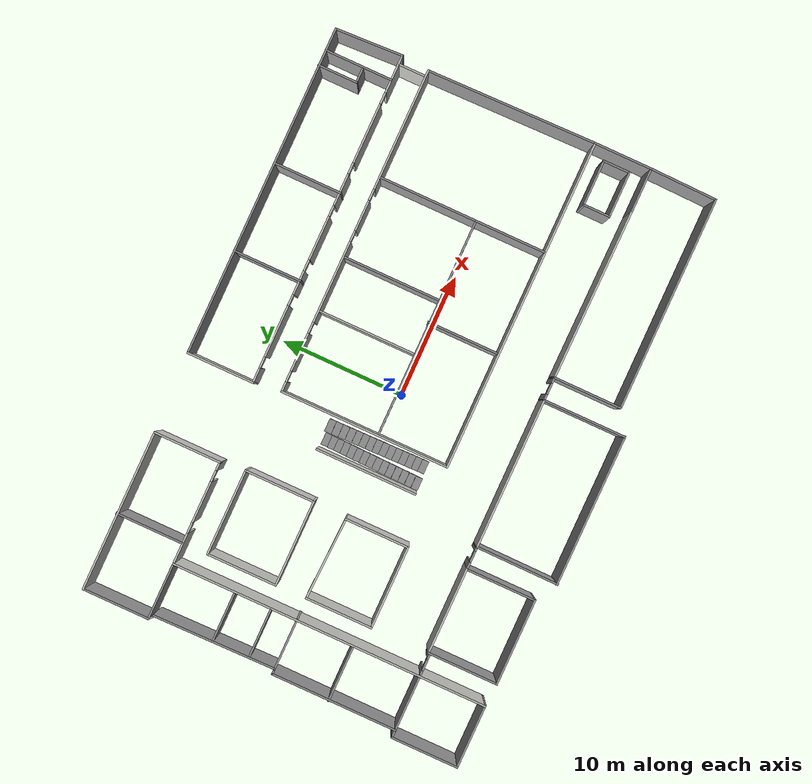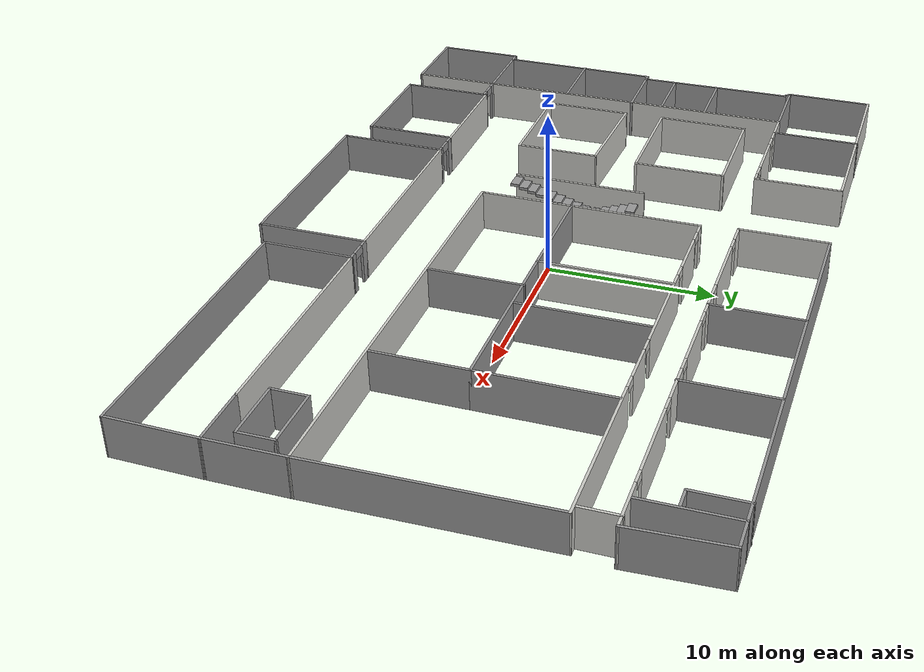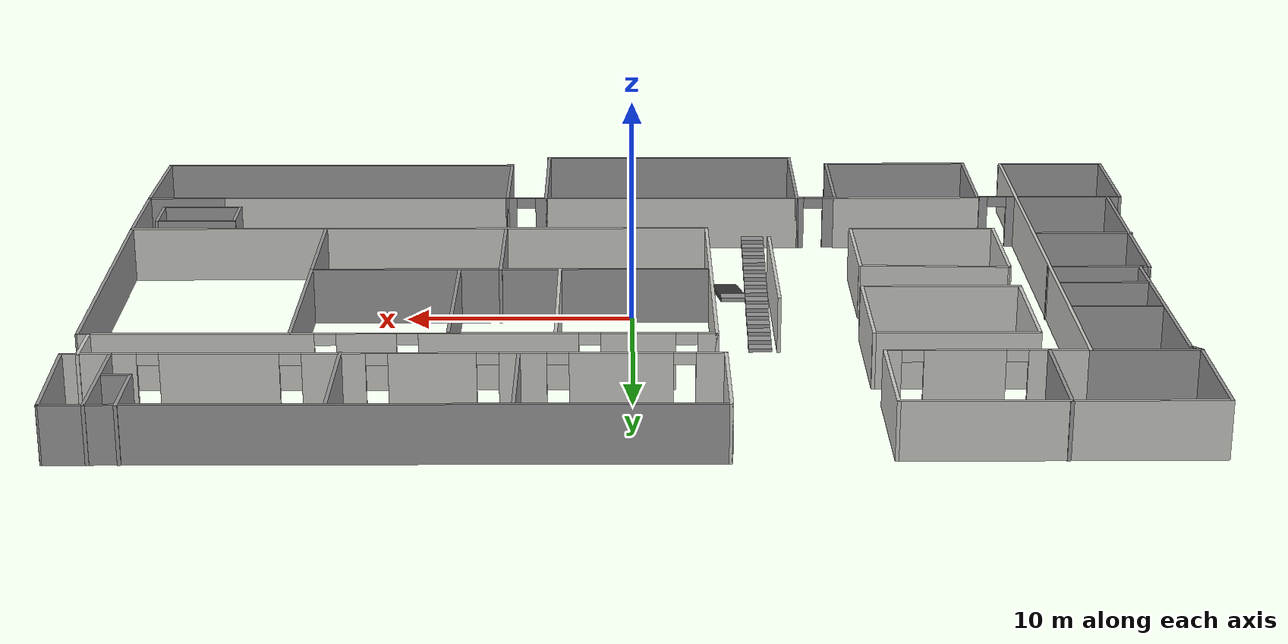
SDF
<?xml version='1.0'?>
<sdf version='1.6'>
  <model name='b1'>
    <pose frame=''>-0.20488 -0.299258 0 0 -0 0</pose>
    <link name='Stairs_0'>
      <visual name='Stairs_0_Visual_0'>
        <pose frame=''>-4.10055 -3.51145 0.083333 0 -0 -3.14159</pose>
        <geometry>
          <box>
            <size>1.0342 0.547943 0.166667</size>
          </box>
        </geometry>
        <material>
          <script>
            <uri>file://media/materials/scripts/gazebo.material</uri>
            <name>Gazebo/Grey</name>
          </script>
          <ambient>1 1 1 1</ambient>
        </material>
      </visual>
      <collision name='Stairs_0_Collision_0'>
        <geometry>
          <box>
            <size>1.0342 0.547943 0.166667</size>
          </box>
        </geometry>
        <pose frame=''>-4.10055 -3.51145 0.083333 0 -0 -3.14159</pose>
      </collision>
      <visual name='Stairs_0_Visual_1'>
        <pose frame=''>-4.10055 -2.96351 0.25 0 -0 -3.14159</pose>
        <geometry>
          <box>
            <size>1.0342 0.547943 0.166667</size>
          </box>
        </geometry>
        <material>
          <script>
            <uri>file://media/materials/scripts/gazebo.material</uri>
            <name>Gazebo/Grey</name>
          </script>
          <ambient>1 1 1 1</ambient>
        </material>
      </visual>
      <collision name='Stairs_0_Collision_1'>
        <geometry>
          <box>
            <size>1.0342 0.547943 0.166667</size>
          </box>
        </geometry>
        <pose frame=''>-4.10055 -2.96351 0.25 0 -0 -3.14159</pose>
      </collision>
      <visual name='Stairs_0_Visual_2'>
        <pose frame=''>-4.10055 -2.41556 0.416667 0 -0 -3.14159</pose>
        <geometry>
          <box>
            <size>1.0342 0.547943 0.166667</size>
          </box>
        </geometry>
        <material>
          <script>
            <uri>file://media/materials/scripts/gazebo.material</uri>
            <name>Gazebo/Grey</name>
          </script>
          <ambient>1 1 1 1</ambient>
        </material>
      </visual>
      <collision name='Stairs_0_Collision_2'>
        <geometry>
          <box>
            <size>1.0342 0.547943 0.166667</size>
          </box>
        </geometry>
        <pose frame=''>-4.10055 -2.41556 0.416667 0 -0 -3.14159</pose>
      </collision>
      <visual name='Stairs_0_Visual_3'>
        <pose frame=''>-4.10055 -1.86762 0.583333 0 -0 -3.14159</pose>
        <geometry>
          <box>
            <size>1.0342 0.547943 0.166667</size>
          </box>
        </geometry>
        <material>
          <script>
            <uri>file://media/materials/scripts/gazebo.material</uri>
            <name>Gazebo/Grey</name>
          </script>
          <ambient>1 1 1 1</ambient>
        </material>
      </visual>
      <collision name='Stairs_0_Collision_3'>
        <geometry>
          <box>
            <size>1.0342 0.547943 0.166667</size>
          </box>
        </geometry>
        <pose frame=''>-4.10055 -1.86762 0.583333 0 -0 -3.14159</pose>
      </collision>
      <visual name='Stairs_0_Visual_4'>
        <pose frame=''>-4.10055 -1.31967 0.75 0 -0 -3.14159</pose>
        <geometry>
          <box>
            <size>1.0342 0.547943 0.166667</size>
          </box>
        </geometry>
        <material>
          <script>
            <uri>file://media/materials/scripts/gazebo.material</uri>
            <name>Gazebo/Grey</name>
          </script>
          <ambient>1 1 1 1</ambient>
        </material>
      </visual>
      <collision name='Stairs_0_Collision_4'>
        <geometry>
          <box>
            <size>1.0342 0.547943 0.166667</size>
          </box>
        </geometry>
        <pose frame=''>-4.10055 -1.31967 0.75 0 -0 -3.14159</pose>
      </collision>
      <visual name='Stairs_0_Visual_5'>
        <pose frame=''>-4.10055 -0.771732 0.916667 0 -0 -3.14159</pose>
        <geometry>
          <box>
            <size>1.0342 0.547943 0.166667</size>
          </box>
        </geometry>
        <material>
          <script>
            <uri>file://media/materials/scripts/gazebo.material</uri>
            <name>Gazebo/Grey</name>
          </script>
          <ambient>1 1 1 1</ambient>
        </material>
      </visual>
      <collision name='Stairs_0_Collision_5'>
        <geometry>
          <box>
            <size>1.0342 0.547943 0.166667</size>
          </box>
        </geometry>
        <pose frame=''>-4.10055 -0.771732 0.916667 0 -0 -3.14159</pose>
      </collision>
      <visual name='Stairs_0_Visual_6'>
        <pose frame=''>-4.10055 -0.223788 1.08333 0 -0 -3.14159</pose>
        <geometry>
          <box>
            <size>1.0342 0.547943 0.166667</size>
          </box>
        </geometry>
        <material>
          <script>
            <uri>file://media/materials/scripts/gazebo.material</uri>
            <name>Gazebo/Grey</name>
          </script>
          <ambient>1 1 1 1</ambient>
        </material>
      </visual>
      <collision name='Stairs_0_Collision_6'>
        <geometry>
          <box>
            <size>1.0342 0.547943 0.166667</size>
          </box>
        </geometry>
        <pose frame=''>-4.10055 -0.223788 1.08333 0 -0 -3.14159</pose>
      </collision>
      <visual name='Stairs_0_Visual_7'>
        <pose frame=''>-4.10055 0.324155 1.25 0 -0 -3.14159</pose>
        <geometry>
          <box>
            <size>1.0342 0.547943 0.166667</size>
          </box>
        </geometry>
        <material>
          <script>
            <uri>file://media/materials/scripts/gazebo.material</uri>
            <name>Gazebo/Grey</name>
          </script>
          <ambient>1 1 1 1</ambient>
        </material>
      </visual>
      <collision name='Stairs_0_Collision_7'>
        <geometry>
          <box>
            <size>1.0342 0.547943 0.166667</size>
          </box>
        </geometry>
        <pose frame=''>-4.10055 0.324155 1.25 0 -0 -3.14159</pose>
      </collision>
      <visual name='Stairs_0_Visual_8'>
        <pose frame=''>-4.10055 0.872098 1.41667 0 -0 -3.14159</pose>
        <geometry>
          <box>
            <size>1.0342 0.547943 0.166667</size>
          </box>
        </geometry>
        <material>
          <script>
            <uri>file://media/materials/scripts/gazebo.material</uri>
            <name>Gazebo/Grey</name>
          </script>
          <ambient>1 1 1 1</ambient>
        </material>
      </visual>
      <collision name='Stairs_0_Collision_8'>
        <geometry>
          <box>
            <size>1.0342 0.547943 0.166667</size>
          </box>
        </geometry>
        <pose frame=''>-4.10055 0.872098 1.41667 0 -0 -3.14159</pose>
      </collision>
      <visual name='Stairs_0_Visual_9'>
        <pose frame=''>-4.10055 1.42004 1.58333 0 -0 -3.14159</pose>
        <geometry>
          <box>
            <size>1.0342 0.547943 0.166667</size>
          </box>
        </geometry>
        <material>
          <script>
            <uri>file://media/materials/scripts/gazebo.material</uri>
            <name>Gazebo/Grey</name>
          </script>
          <ambient>1 1 1 1</ambient>
        </material>
      </visual>
      <collision name='Stairs_0_Collision_9'>
        <geometry>
          <box>
            <size>1.0342 0.547943 0.166667</size>
          </box>
        </geometry>
        <pose frame=''>-4.10055 1.42004 1.58333 0 -0 -3.14159</pose>
      </collision>
      <visual name='Stairs_0_Visual_10'>
        <pose frame=''>-4.10055 1.96799 1.75 0 -0 -3.14159</pose>
        <geometry>
          <box>
            <size>1.0342 0.547943 0.166667</size>
          </box>
        </geometry>
        <material>
          <script>
            <uri>file://media/materials/scripts/gazebo.material</uri>
            <name>Gazebo/Grey</name>
          </script>
          <ambient>1 1 1 1</ambient>
        </material>
      </visual>
      <collision name='Stairs_0_Collision_10'>
        <geometry>
          <box>
            <size>1.0342 0.547943 0.166667</size>
          </box>
        </geometry>
        <pose frame=''>-4.10055 1.96799 1.75 0 -0 -3.14159</pose>
      </collision>
      <visual name='Stairs_0_Visual_11'>
        <pose frame=''>-4.10055 2.51593 1.91667 0 -0 -3.14159</pose>
        <geometry>
          <box>
            <size>1.0342 0.547943 0.166667</size>
          </box>
        </geometry>
        <material>
          <script>
            <uri>file://media/materials/scripts/gazebo.material</uri>
            <name>Gazebo/Grey</name>
          </script>
          <ambient>1 1 1 1</ambient>
        </material>
      </visual>
      <collision name='Stairs_0_Collision_11'>
        <geometry>
          <box>
            <size>1.0342 0.547943 0.166667</size>
          </box>
        </geometry>
        <pose frame=''>-4.10055 2.51593 1.91667 0 -0 -3.14159</pose>
      </collision>
      <visual name='Stairs_0_Visual_12'>
        <pose frame=''>-4.10055 3.06387 2.08333 0 -0 -3.14159</pose>
        <geometry>
          <box>
            <size>1.0342 0.547943 0.166667</size>
          </box>
        </geometry>
        <material>
          <script>
            <uri>file://media/materials/scripts/gazebo.material</uri>
            <name>Gazebo/Grey</name>
          </script>
          <ambient>1 1 1 1</ambient>
        </material>
      </visual>
      <collision name='Stairs_0_Collision_12'>
        <geometry>
          <box>
            <size>1.0342 0.547943 0.166667</size>
          </box>
        </geometry>
        <pose frame=''>-4.10055 3.06387 2.08333 0 -0 -3.14159</pose>
      </collision>
      <visual name='Stairs_0_Visual_13'>
        <pose frame=''>-4.10055 3.61181 2.25 0 -0 -3.14159</pose>
        <geometry>
          <box>
            <size>1.0342 0.547943 0.166667</size>
          </box>
        </geometry>
        <material>
          <script>
            <uri>file://media/materials/scripts/gazebo.material</uri>
            <name>Gazebo/Grey</name>
          </script>
          <ambient>1 1 1 1</ambient>
        </material>
      </visual>
      <collision name='Stairs_0_Collision_13'>
        <geometry>
          <box>
            <size>1.0342 0.547943 0.166667</size>
          </box>
        </geometry>
        <pose frame=''>-4.10055 3.61181 2.25 0 -0 -3.14159</pose>
      </collision>
      <visual name='Stairs_0_Visual_14'>
        <pose frame=''>-4.10055 4.15976 2.41667 0 -0 -3.14159</pose>
        <geometry>
          <box>
            <size>1.0342 0.547943 0.166667</size>
          </box>
        </geometry>
        <material>
          <script>
            <uri>file://media/materials/scripts/gazebo.material</uri>
            <name>Gazebo/Grey</name>
          </script>
          <ambient>1 1 1 1</ambient>
        </material>
      </visual>
      <collision name='Stairs_0_Collision_14'>
        <geometry>
          <box>
            <size>1.0342 0.547943 0.166667</size>
          </box>
        </geometry>
        <pose frame=''>-4.10055 4.15976 2.41667 0 -0 -3.14159</pose>
      </collision>
    </link>
    <link name='Stairs_1'>
      <visual name='Stairs_1_Visual_0'>
        <pose frame=''>-5.30683 4.12843 0.083333 0 -0 0</pose>
        <geometry>
          <box>
            <size>1 0.5427 0.166667</size>
          </box>
        </geometry>
        <material>
          <script>
            <uri>file://media/materials/scripts/gazebo.material</uri>
            <name>Gazebo/Grey</name>
          </script>
          <ambient>1 1 1 1</ambient>
        </material>
      </visual>
      <collision name='Stairs_1_Collision_0'>
        <geometry>
          <box>
            <size>1 0.5427 0.166667</size>
          </box>
        </geometry>
        <pose frame=''>-5.30683 4.12843 0.083333 0 -0 0</pose>
      </collision>
      <visual name='Stairs_1_Visual_1'>
        <pose frame=''>-5.30683 3.58574 0.25 0 -0 0</pose>
        <geometry>
          <box>
            <size>1 0.5427 0.166667</size>
          </box>
        </geometry>
        <material>
          <script>
            <uri>file://media/materials/scripts/gazebo.material</uri>
            <name>Gazebo/Grey</name>
          </script>
          <ambient>1 1 1 1</ambient>
        </material>
      </visual>
      <collision name='Stairs_1_Collision_1'>
        <geometry>
          <box>
            <size>1 0.5427 0.166667</size>
          </box>
        </geometry>
        <pose frame=''>-5.30683 3.58574 0.25 0 -0 0</pose>
      </collision>
      <visual name='Stairs_1_Visual_2'>
        <pose frame=''>-5.30683 3.04304 0.416667 0 -0 0</pose>
        <geometry>
          <box>
            <size>1 0.5427 0.166667</size>
          </box>
        </geometry>
        <material>
          <script>
            <uri>file://media/materials/scripts/gazebo.material</uri>
            <name>Gazebo/Grey</name>
          </script>
          <ambient>1 1 1 1</ambient>
        </material>
      </visual>
      <collision name='Stairs_1_Collision_2'>
        <geometry>
          <box>
            <size>1 0.5427 0.166667</size>
          </box>
        </geometry>
        <pose frame=''>-5.30683 3.04304 0.416667 0 -0 0</pose>
      </collision>
      <visual name='Stairs_1_Visual_3'>
        <pose frame=''>-5.30683 2.50034 0.583333 0 -0 0</pose>
        <geometry>
          <box>
            <size>1 0.5427 0.166667</size>
          </box>
        </geometry>
        <material>
          <script>
            <uri>file://media/materials/scripts/gazebo.material</uri>
            <name>Gazebo/Grey</name>
          </script>
          <ambient>1 1 1 1</ambient>
        </material>
      </visual>
      <collision name='Stairs_1_Collision_3'>
        <geometry>
          <box>
            <size>1 0.5427 0.166667</size>
          </box>
        </geometry>
        <pose frame=''>-5.30683 2.50034 0.583333 0 -0 0</pose>
      </collision>
      <visual name='Stairs_1_Visual_4'>
        <pose frame=''>-5.30683 1.95764 0.75 0 -0 0</pose>
        <geometry>
          <box>
            <size>1 0.5427 0.166667</size>
          </box>
        </geometry>
        <material>
          <script>
            <uri>file://media/materials/scripts/gazebo.material</uri>
            <name>Gazebo/Grey</name>
          </script>
          <ambient>1 1 1 1</ambient>
        </material>
      </visual>
      <collision name='Stairs_1_Collision_4'>
        <geometry>
          <box>
            <size>1 0.5427 0.166667</size>
          </box>
        </geometry>
        <pose frame=''>-5.30683 1.95764 0.75 0 -0 0</pose>
      </collision>
      <visual name='Stairs_1_Visual_5'>
        <pose frame=''>-5.30683 1.41494 0.916667 0 -0 0</pose>
        <geometry>
          <box>
            <size>1 0.5427 0.166667</size>
          </box>
        </geometry>
        <material>
          <script>
            <uri>file://media/materials/scripts/gazebo.material</uri>
            <name>Gazebo/Grey</name>
          </script>
          <ambient>1 1 1 1</ambient>
        </material>
      </visual>
      <collision name='Stairs_1_Collision_5'>
        <geometry>
          <box>
            <size>1 0.5427 0.166667</size>
          </box>
        </geometry>
        <pose frame=''>-5.30683 1.41494 0.916667 0 -0 0</pose>
      </collision>
      <visual name='Stairs_1_Visual_6'>
        <pose frame=''>-5.30683 0.872236 1.08333 0 -0 0</pose>
        <geometry>
          <box>
            <size>1 0.5427 0.166667</size>
          </box>
        </geometry>
        <material>
          <script>
            <uri>file://media/materials/scripts/gazebo.material</uri>
            <name>Gazebo/Grey</name>
          </script>
          <ambient>1 1 1 1</ambient>
        </material>
      </visual>
      <collision name='Stairs_1_Collision_6'>
        <geometry>
          <box>
            <size>1 0.5427 0.166667</size>
          </box>
        </geometry>
        <pose frame=''>-5.30683 0.872236 1.08333 0 -0 0</pose>
      </collision>
      <visual name='Stairs_1_Visual_7'>
        <pose frame=''>-5.30683 0.329537 1.25 0 -0 0</pose>
        <geometry>
          <box>
            <size>1 0.5427 0.166667</size>
          </box>
        </geometry>
        <material>
          <script>
            <uri>file://media/materials/scripts/gazebo.material</uri>
            <name>Gazebo/Grey</name>
          </script>
          <ambient>1 1 1 1</ambient>
        </material>
      </visual>
      <collision name='Stairs_1_Collision_7'>
        <geometry>
          <box>
            <size>1 0.5427 0.166667</size>
          </box>
        </geometry>
        <pose frame=''>-5.30683 0.329537 1.25 0 -0 0</pose>
      </collision>
      <visual name='Stairs_1_Visual_8'>
        <pose frame=''>-5.30683 -0.213163 1.41667 0 -0 0</pose>
        <geometry>
          <box>
            <size>1 0.5427 0.166667</size>
          </box>
        </geometry>
        <material>
          <script>
            <uri>file://media/materials/scripts/gazebo.material</uri>
            <name>Gazebo/Grey</name>
          </script>
          <ambient>1 1 1 1</ambient>
        </material>
      </visual>
      <collision name='Stairs_1_Collision_8'>
        <geometry>
          <box>
            <size>1 0.5427 0.166667</size>
          </box>
        </geometry>
        <pose frame=''>-5.30683 -0.213163 1.41667 0 -0 0</pose>
      </collision>
      <visual name='Stairs_1_Visual_9'>
        <pose frame=''>-5.30683 -0.755863 1.58333 0 -0 0</pose>
        <geometry>
          <box>
            <size>1 0.5427 0.166667</size>
          </box>
        </geometry>
        <material>
          <script>
            <uri>file://media/materials/scripts/gazebo.material</uri>
            <name>Gazebo/Grey</name>
          </script>
          <ambient>1 1 1 1</ambient>
        </material>
      </visual>
      <collision name='Stairs_1_Collision_9'>
        <geometry>
          <box>
            <size>1 0.5427 0.166667</size>
          </box>
        </geometry>
        <pose frame=''>-5.30683 -0.755863 1.58333 0 -0 0</pose>
      </collision>
      <visual name='Stairs_1_Visual_10'>
        <pose frame=''>-5.30683 -1.29856 1.75 0 -0 0</pose>
        <geometry>
          <box>
            <size>1 0.5427 0.166667</size>
          </box>
        </geometry>
        <material>
          <script>
            <uri>file://media/materials/scripts/gazebo.material</uri>
            <name>Gazebo/Grey</name>
          </script>
          <ambient>1 1 1 1</ambient>
        </material>
      </visual>
      <collision name='Stairs_1_Collision_10'>
        <geometry>
          <box>
            <size>1 0.5427 0.166667</size>
          </box>
        </geometry>
        <pose frame=''>-5.30683 -1.29856 1.75 0 -0 0</pose>
      </collision>
      <visual name='Stairs_1_Visual_11'>
        <pose frame=''>-5.30683 -1.84126 1.91667 0 -0 0</pose>
        <geometry>
          <box>
            <size>1 0.5427 0.166667</size>
          </box>
        </geometry>
        <material>
          <script>
            <uri>file://media/materials/scripts/gazebo.material</uri>
            <name>Gazebo/Grey</name>
          </script>
          <ambient>1 1 1 1</ambient>
        </material>
      </visual>
      <collision name='Stairs_1_Collision_11'>
        <geometry>
          <box>
            <size>1 0.5427 0.166667</size>
          </box>
        </geometry>
        <pose frame=''>-5.30683 -1.84126 1.91667 0 -0 0</pose>
      </collision>
      <visual name='Stairs_1_Visual_12'>
        <pose frame=''>-5.30683 -2.38396 2.08333 0 -0 0</pose>
        <geometry>
          <box>
            <size>1 0.5427 0.166667</size>
          </box>
        </geometry>
        <material>
          <script>
            <uri>file://media/materials/scripts/gazebo.material</uri>
            <name>Gazebo/Grey</name>
          </script>
          <ambient>1 1 1 1</ambient>
        </material>
      </visual>
      <collision name='Stairs_1_Collision_12'>
        <geometry>
          <box>
            <size>1 0.5427 0.166667</size>
          </box>
        </geometry>
        <pose frame=''>-5.30683 -2.38396 2.08333 0 -0 0</pose>
      </collision>
      <visual name='Stairs_1_Visual_13'>
        <pose frame=''>-5.30683 -2.92666 2.25 0 -0 0</pose>
        <geometry>
          <box>
            <size>1 0.5427 0.166667</size>
          </box>
        </geometry>
        <material>
          <script>
            <uri>file://media/materials/scripts/gazebo.material</uri>
            <name>Gazebo/Grey</name>
          </script>
          <ambient>1 1 1 1</ambient>
        </material>
      </visual>
      <collision name='Stairs_1_Collision_13'>
        <geometry>
          <box>
            <size>1 0.5427 0.166667</size>
          </box>
        </geometry>
        <pose frame=''>-5.30683 -2.92666 2.25 0 -0 0</pose>
      </collision>
      <visual name='Stairs_1_Visual_14'>
        <pose frame=''>-5.30683 -3.46936 2.41667 0 -0 0</pose>
        <geometry>
          <box>
            <size>1 0.5427 0.166667</size>
          </box>
        </geometry>
        <material>
          <script>
            <uri>file://media/materials/scripts/gazebo.material</uri>
            <name>Gazebo/Grey</name>
          </script>
          <ambient>1 1 1 1</ambient>
        </material>
      </visual>
      <collision name='Stairs_1_Collision_14'>
        <geometry>
          <box>
            <size>1 0.5427 0.166667</size>
          </box>
        </geometry>
        <pose frame=''>-5.30683 -3.46936 2.41667 0 -0 0</pose>
      </collision>
    </link>
    <link name='Wall_0'>
      <collision name='Wall_0_Collision'>
        <geometry>
          <box>
            <size>25.75 0.15 2.5</size>
          </box>
        </geometry>
        <pose frame=''>0 0 1.25 0 -0 0</pose>
      </collision>
      <visual name='Wall_0_Visual'>
        <pose frame=''>0 0 1.25 0 -0 0</pose>
        <geometry>
          <box>
            <size>25.75 0.15 2.5</size>
          </box>
        </geometry>
        <material>
          <script>
            <uri>file://media/materials/scripts/gazebo.material</uri>
            <name>Gazebo/CeilingTiled</name>
          </script>
          <ambient>1 1 1 1</ambient>
        </material>
      </visual>
      <pose frame=''>-18.3333 -2.23544 0 0 0 -1.5708</pose>
    </link>
    <link name='Wall_10'>
      <collision name='Wall_10_Collision'>
        <geometry>
          <box>
            <size>12.2312 0.15 2.5</size>
          </box>
        </geometry>
        <pose frame=''>0 0 1.25 0 -0 0</pose>
      </collision>
      <visual name='Wall_10_Visual'>
        <pose frame=''>0 0 1.25 0 -0 0</pose>
        <geometry>
          <box>
            <size>12.2312 0.15 2.5</size>
          </box>
        </geometry>
        <material>
          <script>
            <uri>file://media/materials/scripts/gazebo.material</uri>
            <name>Gazebo/CeilingTiled</name>
          </script>
          <ambient>1 1 1 1</ambient>
        </material>
      </visual>
      <pose frame=''>-1.74049 -9.5555 0 0 -0 0</pose>
    </link>
    <link name='Wall_101'>
      <collision name='Wall_101_Collision'>
        <geometry>
          <box>
            <size>7.75 0.15 2.5</size>
          </box>
        </geometry>
        <pose frame=''>0 0 1.25 0 -0 0</pose>
      </collision>
      <visual name='Wall_101_Visual'>
        <pose frame=''>0 0 1.25 0 -0 0</pose>
        <geometry>
          <box>
            <size>7.75 0.15 2.5</size>
          </box>
        </geometry>
        <material>
          <script>
            <uri>file://media/materials/scripts/gazebo.material</uri>
            <name>Gazebo/Grey</name>
          </script>
          <ambient>1 1 1 1</ambient>
        </material>
      </visual>
      <pose frame=''>7.82846 4.59998 0 0 0 -1.5708</pose>
    </link>
    <link name='Wall_103'>
      <collision name='Wall_103_Collision'>
        <geometry>
          <box>
            <size>5.75 0.15 2.5</size>
          </box>
        </geometry>
        <pose frame=''>0 0 1.25 0 -0 0</pose>
      </collision>
      <visual name='Wall_103_Visual'>
        <pose frame=''>0 0 1.25 0 -0 0</pose>
        <geometry>
          <box>
            <size>5.75 0.15 2.5</size>
          </box>
        </geometry>
        <material>
          <script>
            <uri>file://media/materials/scripts/gazebo.material</uri>
            <name>Gazebo/Grey</name>
          </script>
          <ambient>1 1 1 1</ambient>
        </material>
      </visual>
      <pose frame=''>14.3596 -2.15208 0 0 0 -1.5708</pose>
    </link>
    <link name='Wall_105'>
      <collision name='Wall_105_Collision'>
        <geometry>
          <box>
            <size>5.75 0.15 2.5</size>
          </box>
        </geometry>
        <pose frame=''>0 0 1.25 0 -0 0</pose>
      </collision>
      <visual name='Wall_105_Visual'>
        <pose frame=''>0 0 1.25 0 -0 0</pose>
        <geometry>
          <box>
            <size>5.75 0.15 2.5</size>
          </box>
        </geometry>
        <material>
          <script>
            <uri>file://media/materials/scripts/gazebo.material</uri>
            <name>Gazebo/Grey</name>
          </script>
          <ambient>1 1 1 1</ambient>
        </material>
      </visual>
      <pose frame=''>6.01579 -2.07494 0 0 0 -1.5708</pose>
    </link>
    <link name='Wall_11'>
      <collision name='Wall_11_Collision'>
        <geometry>
          <box>
            <size>6.75 0.15 2.5</size>
          </box>
        </geometry>
        <pose frame=''>0 0 1.25 0 -0 0</pose>
      </collision>
      <visual name='Wall_11_Visual'>
        <pose frame=''>0 0 1.25 0 -0 0</pose>
        <geometry>
          <box>
            <size>6.75 0.15 2.5</size>
          </box>
        </geometry>
        <material>
          <script>
            <uri>file://media/materials/scripts/gazebo.material</uri>
            <name>Gazebo/Grey</name>
          </script>
          <ambient>1 1 1 1</ambient>
        </material>
      </visual>
      <pose frame=''>4.30011 -12.8555 0 0 0 -1.5708</pose>
    </link>
    <link name='Wall_12'>
      <collision name='Wall_12_Collision'>
        <geometry>
          <box>
            <size>12.2877 0.15 2.5</size>
          </box>
        </geometry>
        <pose frame=''>0 0 1.25 0 -0 0</pose>
      </collision>
      <visual name='Wall_12_Visual'>
        <pose frame=''>0 0 1.25 0 -0 0</pose>
        <geometry>
          <box>
            <size>12.2877 0.15 2.5</size>
          </box>
        </geometry>
        <material>
          <script>
            <uri>file://media/materials/scripts/gazebo.material</uri>
            <name>Gazebo/Grey</name>
          </script>
          <ambient>1 1 1 1</ambient>
        </material>
      </visual>
      <pose frame=''>-1.74989 -16.1555 0 0 -0 3.13849</pose>
    </link>
    <link name='Wall_13'>
      <collision name='Wall_13_Collision'>
        <geometry>
          <box>
            <size>6.75 0.15 2.5</size>
          </box>
        </geometry>
        <pose frame=''>0 0 1.25 0 -0 0</pose>
      </collision>
      <visual name='Wall_13_Visual'>
        <pose frame=''>0 0 1.25 0 -0 0</pose>
        <geometry>
          <box>
            <size>6.75 0.15 2.5</size>
          </box>
        </geometry>
        <material>
          <script>
            <uri>file://media/materials/scripts/gazebo.material</uri>
            <name>Gazebo/Grey</name>
          </script>
          <ambient>1 1 1 1</ambient>
        </material>
      </visual>
      <pose frame=''>-7.78109 -12.8555 0 0 -0 1.5651</pose>
    </link>
    <link name='Wall_15'>
      <collision name='Wall_15_Collision'>
        <geometry>
          <box>
            <size>5.58386 0.15 2.5</size>
          </box>
        </geometry>
        <pose frame=''>0 0 1.25 0 -0 0</pose>
      </collision>
      <visual name='Wall_15_Visual'>
        <pose frame=''>0 0 1.25 0 -0 0</pose>
        <geometry>
          <box>
            <size>5.58386 0.15 2.5</size>
          </box>
        </geometry>
        <material>
          <script>
            <uri>file://media/materials/scripts/gazebo.material</uri>
            <name>Gazebo/Grey</name>
          </script>
          <ambient>1 1 1 1</ambient>
        </material>
      </visual>
      <pose frame=''>6.14467 -12.2724 0 0 -0 1.56879</pose>
    </link>
    <link name='Wall_16'>
      <collision name='Wall_16_Collision'>
        <geometry>
          <box>
            <size>13.7394 0.15 2.5</size>
          </box>
        </geometry>
        <pose frame=''>0 0 1.25 0 -0 0</pose>
      </collision>
      <visual name='Wall_16_Visual'>
        <pose frame=''>0 0 1.25 0 -0 0</pose>
        <geometry>
          <box>
            <size>13.7394 0.15 2.5</size>
          </box>
        </geometry>
        <material>
          <script>
            <uri>file://media/materials/scripts/gazebo.material</uri>
            <name>Gazebo/CeilingTiled</name>
          </script>
          <ambient>1 1 1 1</ambient>
        </material>
      </visual>
      <pose frame=''>12.9447 -9.59742 0 0 0 -0.00617</pose>
    </link>
    <link name='Wall_17'>
      <collision name='Wall_17_Collision'>
        <geometry>
          <box>
            <size>3.75 0.15 2.5</size>
          </box>
        </geometry>
        <pose frame=''>0 0 1.25 0 -0 0</pose>
      </collision>
      <visual name='Wall_17_Visual'>
        <pose frame=''>0 0 1.25 0 -0 0</pose>
        <geometry>
          <box>
            <size>3.75 0.15 2.5</size>
          </box>
        </geometry>
        <material>
          <script>
            <uri>file://media/materials/scripts/gazebo.material</uri>
            <name>Gazebo/Grey</name>
          </script>
          <ambient>1 1 1 1</ambient>
        </material>
      </visual>
      <pose frame=''>21.5392 -9.63935 0 0 -0 0</pose>
    </link>
    <link name='Wall_18'>
      <collision name='Wall_18_Collision'>
        <geometry>
          <box>
            <size>4.75 0.15 2.5</size>
          </box>
        </geometry>
        <pose frame=''>0 0 1.25 0 -0 0</pose>
      </collision>
      <visual name='Wall_18_Visual'>
        <pose frame=''>0 0 1.25 0 -0 0</pose>
        <geometry>
          <box>
            <size>4.75 0.15 2.5</size>
          </box>
        </geometry>
        <material>
          <script>
            <uri>file://media/materials/scripts/gazebo.material</uri>
            <name>Gazebo/Grey</name>
          </script>
          <ambient>1 1 1 1</ambient>
        </material>
      </visual>
      <pose frame=''>23.3392 -7.33935 0 0 -0 1.5708</pose>
    </link>
    <link name='Wall_19'>
      <collision name='Wall_19_Collision'>
        <geometry>
          <box>
            <size>26.75 0.15 2.5</size>
          </box>
        </geometry>
        <pose frame=''>0 0 1.25 0 -0 0</pose>
      </collision>
      <visual name='Wall_19_Visual'>
        <pose frame=''>0 0 1.25 0 -0 0</pose>
        <geometry>
          <box>
            <size>26.75 0.15 2.5</size>
          </box>
        </geometry>
        <material>
          <script>
            <uri>file://media/materials/scripts/gazebo.material</uri>
            <name>Gazebo/CeilingTiled</name>
          </script>
          <ambient>1 1 1 1</ambient>
        </material>
      </visual>
      <pose frame=''>10.0392 -5.03935 0 0 -0 3.14159</pose>
    </link>
    <link name='Wall_2'>
      <collision name='Wall_2_Collision'>
        <geometry>
          <box>
            <size>5.5 0.15 2.5</size>
          </box>
        </geometry>
        <pose frame=''>0 0 1.25 0 -0 0</pose>
      </collision>
      <visual name='Wall_2_Visual'>
        <pose frame=''>0 0 1.25 0 -0 0</pose>
        <geometry>
          <box>
            <size>5.5 0.15 2.5</size>
          </box>
        </geometry>
        <material>
          <script>
            <uri>file://media/materials/scripts/gazebo.material</uri>
            <name>Gazebo/CeilingTiled</name>
          </script>
          <ambient>1 1 1 1</ambient>
        </material>
      </visual>
      <pose frame=''>-3.54517 13.4609 0 0 0 -1.5708</pose>
    </link>
    <link name='Wall_21'>
      <collision name='Wall_21_Collision'>
        <geometry>
          <box>
            <size>13.75 0.15 2.5</size>
          </box>
        </geometry>
        <pose frame=''>0 0 1.25 0 -0 0</pose>
      </collision>
      <visual name='Wall_21_Visual'>
        <pose frame=''>0 0 1.25 0 -0 0</pose>
        <geometry>
          <box>
            <size>13.75 0.15 2.5</size>
          </box>
        </geometry>
        <material>
          <script>
            <uri>file://media/materials/scripts/gazebo.material</uri>
            <name>Gazebo/CeilingTiled</name>
          </script>
          <ambient>1 1 1 1</ambient>
        </material>
      </visual>
      <pose frame=''>-3.26078 1.76065 0 0 -0 1.5708</pose>
    </link>
    <link name='Wall_22'>
      <pose frame=''>9.91422 8.56065 0 0 -0 0</pose>
      <visual name='Wall_22_Visual_0'>
        <pose frame=''>-12.8162 0 1.25 0 -0 0</pose>
        <geometry>
          <box>
            <size>0.867558 0.15 2.5</size>
          </box>
        </geometry>
        <material>
          <script>
            <uri>file://media/materials/scripts/gazebo.material</uri>
            <name>Gazebo/CeilingTiled</name>
          </script>
          <ambient>1 1 1 1</ambient>
        </material>
      </visual>
      <collision name='Wall_22_Collision_0'>
        <geometry>
          <box>
            <size>0.867558 0.15 2.5</size>
          </box>
        </geometry>
        <pose frame=''>-12.8162 0 1.25 0 -0 0</pose>
      </collision>
      <visual name='Wall_22_Visual_1'>
        <pose frame=''>-9.93193 0 1.25 0 -0 0</pose>
        <geometry>
          <box>
            <size>3.10102 0.15 2.5</size>
          </box>
        </geometry>
        <material>
          <script>
            <uri>file://media/materials/scripts/gazebo.material</uri>
            <name>Gazebo/CeilingTiled</name>
          </script>
          <ambient>1 1 1 1</ambient>
        </material>
      </visual>
      <collision name='Wall_22_Collision_1'>
        <geometry>
          <box>
            <size>3.10102 0.15 2.5</size>
          </box>
        </geometry>
        <pose frame=''>-9.93193 0 1.25 0 -0 0</pose>
      </collision>
      <visual name='Wall_22_Visual_2'>
        <pose frame=''>-4.16979 0 1.25 0 -0 0</pose>
        <geometry>
          <box>
            <size>6.62328 0.15 2.5</size>
          </box>
        </geometry>
        <material>
          <script>
            <uri>file://media/materials/scripts/gazebo.material</uri>
            <name>Gazebo/CeilingTiled</name>
          </script>
          <ambient>1 1 1 1</ambient>
        </material>
      </visual>
      <collision name='Wall_22_Collision_2'>
        <geometry>
          <box>
            <size>6.62328 0.15 2.5</size>
          </box>
        </geometry>
        <pose frame=''>-4.16979 0 1.25 0 -0 0</pose>
      </collision>
      <visual name='Wall_22_Visual_3'>
        <pose frame=''>1.28459 0 1.25 0 -0 0</pose>
        <geometry>
          <box>
            <size>2.48548 0.15 2.5</size>
          </box>
        </geometry>
        <material>
          <script>
            <uri>file://media/materials/scripts/gazebo.material</uri>
            <name>Gazebo/CeilingTiled</name>
          </script>
          <ambient>1 1 1 1</ambient>
        </material>
      </visual>
      <collision name='Wall_22_Collision_3'>
        <geometry>
          <box>
            <size>2.48548 0.15 2.5</size>
          </box>
        </geometry>
        <pose frame=''>1.28459 0 1.25 0 -0 0</pose>
      </collision>
      <visual name='Wall_22_Visual_4'>
        <pose frame=''>8.33867 0 1.25 0 -0 0</pose>
        <geometry>
          <box>
            <size>9.82267 0.15 2.5</size>
          </box>
        </geometry>
        <material>
          <script>
            <uri>file://media/materials/scripts/gazebo.material</uri>
            <name>Gazebo/CeilingTiled</name>
          </script>
          <ambient>1 1 1 1</ambient>
        </material>
      </visual>
      <collision name='Wall_22_Collision_4'>
        <geometry>
          <box>
            <size>9.82267 0.15 2.5</size>
          </box>
        </geometry>
        <pose frame=''>8.33867 0 1.25 0 -0 0</pose>
      </collision>
      <visual name='Wall_22_Visual_5'>
        <pose frame=''>-11.9324 0 2.25 0 -0 0</pose>
        <geometry>
          <box>
            <size>0.9 0.15 0.5</size>
          </box>
        </geometry>
        <material>
          <script>
            <uri>file://media/materials/scripts/gazebo.material</uri>
            <name>Gazebo/CeilingTiled</name>
          </script>
          <ambient>1 1 1 1</ambient>
        </material>
      </visual>
      <collision name='Wall_22_Collision_5'>
        <geometry>
          <box>
            <size>0.9 0.15 0.5</size>
          </box>
        </geometry>
        <pose frame=''>-11.9324 0 2.25 0 -0 0</pose>
      </collision>
      <visual name='Wall_22_Visual_6'>
        <pose frame=''>-7.93142 0 2.25 0 -0 0</pose>
        <geometry>
          <box>
            <size>0.9 0.15 0.5</size>
          </box>
        </geometry>
        <material>
          <script>
            <uri>file://media/materials/scripts/gazebo.material</uri>
            <name>Gazebo/CeilingTiled</name>
          </script>
          <ambient>1 1 1 1</ambient>
        </material>
      </visual>
      <collision name='Wall_22_Collision_6'>
        <geometry>
          <box>
            <size>0.9 0.15 0.5</size>
          </box>
        </geometry>
        <pose frame=''>-7.93142 0 2.25 0 -0 0</pose>
      </collision>
      <visual name='Wall_22_Visual_7'>
        <pose frame=''>-0.408145 0 2.25 0 -0 0</pose>
        <geometry>
          <box>
            <size>0.9 0.15 0.5</size>
          </box>
        </geometry>
        <material>
          <script>
            <uri>file://media/materials/scripts/gazebo.material</uri>
            <name>Gazebo/CeilingTiled</name>
          </script>
          <ambient>1 1 1 1</ambient>
        </material>
      </visual>
      <collision name='Wall_22_Collision_7'>
        <geometry>
          <box>
            <size>0.9 0.15 0.5</size>
          </box>
        </geometry>
        <pose frame=''>-0.408145 0 2.25 0 -0 0</pose>
      </collision>
      <visual name='Wall_22_Visual_8'>
        <pose frame=''>2.97733 0 2.25 0 -0 0</pose>
        <geometry>
          <box>
            <size>0.9 0.15 0.5</size>
          </box>
        </geometry>
        <material>
          <script>
            <uri>file://media/materials/scripts/gazebo.material</uri>
            <name>Gazebo/CeilingTiled</name>
          </script>
          <ambient>1 1 1 1</ambient>
        </material>
      </visual>
      <collision name='Wall_22_Collision_8'>
        <geometry>
          <box>
            <size>0.9 0.15 0.5</size>
          </box>
        </geometry>
        <pose frame=''>2.97733 0 2.25 0 -0 0</pose>
      </collision>
    </link>
    <link name='Wall_23'>
      <collision name='Wall_23_Collision'>
        <geometry>
          <box>
            <size>13.7523 0.15 2.5</size>
          </box>
        </geometry>
        <pose frame=''>0 0 1.25 0 -0 0</pose>
      </collision>
      <visual name='Wall_23_Visual'>
        <pose frame=''>0 0 1.25 0 -0 0</pose>
        <geometry>
          <box>
            <size>13.7523 0.15 2.5</size>
          </box>
        </geometry>
        <material>
          <script>
            <uri>file://media/materials/scripts/gazebo.material</uri>
            <name>Gazebo/Grey</name>
          </script>
          <ambient>1 1 1 1</ambient>
        </material>
      </visual>
      <pose frame=''>23.2142 1.76065 0 0 0 -1.55242</pose>
    </link>
    <link name='Wall_25'>
      <pose frame=''>-14.1583 10.5646 0 0 -0 0</pose>
      <visual name='Wall_25_Visual_0'>
        <pose frame=''>-2.95406 0 1.25 0 -0 0</pose>
        <geometry>
          <box>
            <size>2.59187 0.15 2.5</size>
          </box>
        </geometry>
        <material>
          <script>
            <uri>file://media/materials/scripts/gazebo.material</uri>
            <name>Gazebo/CeilingTiled</name>
          </script>
          <ambient>1 1 1 1</ambient>
        </material>
      </visual>
      <collision name='Wall_25_Collision_0'>
        <geometry>
          <box>
            <size>2.59187 0.15 2.5</size>
          </box>
        </geometry>
        <pose frame=''>-2.95406 0 1.25 0 -0 0</pose>
      </collision>
      <visual name='Wall_25_Visual_1'>
        <pose frame=''>0.915135 0 1.25 0 -0 0</pose>
        <geometry>
          <box>
            <size>3.34653 0.15 2.5</size>
          </box>
        </geometry>
        <material>
          <script>
            <uri>file://media/materials/scripts/gazebo.material</uri>
            <name>Gazebo/CeilingTiled</name>
          </script>
          <ambient>1 1 1 1</ambient>
        </material>
      </visual>
      <collision name='Wall_25_Collision_1'>
        <geometry>
          <box>
            <size>3.34653 0.15 2.5</size>
          </box>
        </geometry>
        <pose frame=''>0.915135 0 1.25 0 -0 0</pose>
      </collision>
      <visual name='Wall_25_Visual_2'>
        <pose frame=''>3.8692 0 1.25 0 -0 0</pose>
        <geometry>
          <box>
            <size>0.7616 0.15 2.5</size>
          </box>
        </geometry>
        <material>
          <script>
            <uri>file://media/materials/scripts/gazebo.material</uri>
            <name>Gazebo/CeilingTiled</name>
          </script>
          <ambient>1 1 1 1</ambient>
        </material>
      </visual>
      <collision name='Wall_25_Collision_2'>
        <geometry>
          <box>
            <size>0.7616 0.15 2.5</size>
          </box>
        </geometry>
        <pose frame=''>3.8692 0 1.25 0 -0 0</pose>
      </collision>
      <visual name='Wall_25_Visual_3'>
        <pose frame=''>-1.20813 0 2.25 0 -0 0</pose>
        <geometry>
          <box>
            <size>0.9 0.15 0.5</size>
          </box>
        </geometry>
        <material>
          <script>
            <uri>file://media/materials/scripts/gazebo.material</uri>
            <name>Gazebo/CeilingTiled</name>
          </script>
          <ambient>1 1 1 1</ambient>
        </material>
      </visual>
      <collision name='Wall_25_Collision_3'>
        <geometry>
          <box>
            <size>0.9 0.15 0.5</size>
          </box>
        </geometry>
        <pose frame=''>-1.20813 0 2.25 0 -0 0</pose>
      </collision>
      <visual name='Wall_25_Visual_4'>
        <pose frame=''>3.0384 0 2.25 0 -0 0</pose>
        <geometry>
          <box>
            <size>0.9 0.15 0.5</size>
          </box>
        </geometry>
        <material>
          <script>
            <uri>file://media/materials/scripts/gazebo.material</uri>
            <name>Gazebo/CeilingTiled</name>
          </script>
          <ambient>1 1 1 1</ambient>
        </material>
      </visual>
      <collision name='Wall_25_Collision_4'>
        <geometry>
          <box>
            <size>0.9 0.15 0.5</size>
          </box>
        </geometry>
        <pose frame=''>3.0384 0 2.25 0 -0 0</pose>
      </collision>
    </link>
    <link name='Wall_26'>
      <collision name='Wall_26_Collision'>
        <geometry>
          <box>
            <size>5.5 0.15 2.5</size>
          </box>
        </geometry>
        <pose frame=''>0 0 1.25 0 -0 0</pose>
      </collision>
      <visual name='Wall_26_Visual'>
        <pose frame=''>0 0 1.25 0 -0 0</pose>
        <geometry>
          <box>
            <size>5.5 0.15 2.5</size>
          </box>
        </geometry>
        <material>
          <script>
            <uri>file://media/materials/scripts/gazebo.material</uri>
            <name>Gazebo/CeilingTiled</name>
          </script>
          <ambient>1 1 1 1</ambient>
        </material>
      </visual>
      <pose frame=''>-9.98326 13.2396 0 0 -0 1.5708</pose>
    </link>
    <link name='Wall_27'>
      <collision name='Wall_27_Collision'>
        <geometry>
          <box>
            <size>13 0.15 2.5</size>
          </box>
        </geometry>
        <pose frame=''>0 0 1.25 0 -0 0</pose>
      </collision>
      <visual name='Wall_27_Visual'>
        <pose frame=''>0 0 1.25 0 -0 0</pose>
        <geometry>
          <box>
            <size>13 0.15 2.5</size>
          </box>
        </geometry>
        <material>
          <script>
            <uri>file://media/materials/scripts/gazebo.material</uri>
            <name>Gazebo/CeilingTiled</name>
          </script>
          <ambient>1 1 1 1</ambient>
        </material>
      </visual>
      <pose frame=''>-16.4083 15.9146 0 0 -0 3.14159</pose>
    </link>
    <link name='Wall_29'>
      <collision name='Wall_29_Collision'>
        <geometry>
          <box>
            <size>5.5 0.15 2.5</size>
          </box>
        </geometry>
        <pose frame=''>0 0 1.25 0 -0 0</pose>
      </collision>
      <visual name='Wall_29_Visual'>
        <pose frame=''>0 0 1.25 0 -0 0</pose>
        <geometry>
          <box>
            <size>5.5 0.15 2.5</size>
          </box>
        </geometry>
        <material>
          <script>
            <uri>file://media/materials/scripts/gazebo.material</uri>
            <name>Gazebo/CeilingTiled</name>
          </script>
          <ambient>1 1 1 1</ambient>
        </material>
      </visual>
      <pose frame=''>-16.5334 -2.20008 0 0 0 -1.5708</pose>
    </link>
    <link name='Wall_3'>
      <pose frame=''>9.87983 10.7859 0 0 -0 0</pose>
      <visual name='Wall_3_Visual_0'>
        <pose frame=''>-12.8556 0 1.25 0 -0 0</pose>
        <geometry>
          <box>
            <size>1.28873 0.15 2.5</size>
          </box>
        </geometry>
        <material>
          <script>
            <uri>file://media/materials/scripts/gazebo.material</uri>
            <name>Gazebo/CeilingTiled</name>
          </script>
          <ambient>1 1 1 1</ambient>
        </material>
      </visual>
      <collision name='Wall_3_Collision_0'>
        <geometry>
          <box>
            <size>1.28873 0.15 2.5</size>
          </box>
        </geometry>
        <pose frame=''>-12.8556 0 1.25 0 -0 0</pose>
      </collision>
      <visual name='Wall_3_Visual_1'>
        <pose frame=''>-9.19651 0 1.25 0 -0 0</pose>
        <geometry>
          <box>
            <size>4.22951 0.15 2.5</size>
          </box>
        </geometry>
        <material>
          <script>
            <uri>file://media/materials/scripts/gazebo.material</uri>
            <name>Gazebo/CeilingTiled</name>
          </script>
          <ambient>1 1 1 1</ambient>
        </material>
      </visual>
      <collision name='Wall_3_Collision_1'>
        <geometry>
          <box>
            <size>4.22951 0.15 2.5</size>
          </box>
        </geometry>
        <pose frame=''>-9.19651 0 1.25 0 -0 0</pose>
      </collision>
      <visual name='Wall_3_Visual_2'>
        <pose frame=''>-5.2126 0 1.25 0 -0 0</pose>
        <geometry>
          <box>
            <size>1.93833 0.15 2.5</size>
          </box>
        </geometry>
        <material>
          <script>
            <uri>file://media/materials/scripts/gazebo.material</uri>
            <name>Gazebo/CeilingTiled</name>
          </script>
          <ambient>1 1 1 1</ambient>
        </material>
      </visual>
      <collision name='Wall_3_Collision_2'>
        <geometry>
          <box>
            <size>1.93833 0.15 2.5</size>
          </box>
        </geometry>
        <pose frame=''>-5.2126 0 1.25 0 -0 0</pose>
      </collision>
      <visual name='Wall_3_Visual_3'>
        <pose frame=''>-1.55355 0 1.25 0 -0 0</pose>
        <geometry>
          <box>
            <size>3.57977 0.15 2.5</size>
          </box>
        </geometry>
        <material>
          <script>
            <uri>file://media/materials/scripts/gazebo.material</uri>
            <name>Gazebo/CeilingTiled</name>
          </script>
          <ambient>1 1 1 1</ambient>
        </material>
      </visual>
      <collision name='Wall_3_Collision_3'>
        <geometry>
          <box>
            <size>3.57977 0.15 2.5</size>
          </box>
        </geometry>
        <pose frame=''>-1.55355 0 1.25 0 -0 0</pose>
      </collision>
      <visual name='Wall_3_Visual_4'>
        <pose frame=''>2.43037 0 1.25 0 -0 0</pose>
        <geometry>
          <box>
            <size>2.58807 0.15 2.5</size>
          </box>
        </geometry>
        <material>
          <script>
            <uri>file://media/materials/scripts/gazebo.material</uri>
            <name>Gazebo/CeilingTiled</name>
          </script>
          <ambient>1 1 1 1</ambient>
        </material>
      </visual>
      <collision name='Wall_3_Collision_4'>
        <geometry>
          <box>
            <size>2.58807 0.15 2.5</size>
          </box>
        </geometry>
        <pose frame=''>2.43037 0 1.25 0 -0 0</pose>
      </collision>
      <visual name='Wall_3_Visual_5'>
        <pose frame=''>7.04693 0 1.25 0 -0 0</pose>
        <geometry>
          <box>
            <size>4.84505 0.15 2.5</size>
          </box>
        </geometry>
        <material>
          <script>
            <uri>file://media/materials/scripts/gazebo.material</uri>
            <name>Gazebo/CeilingTiled</name>
          </script>
          <ambient>1 1 1 1</ambient>
        </material>
      </visual>
      <collision name='Wall_3_Collision_5'>
        <geometry>
          <box>
            <size>4.84505 0.15 2.5</size>
          </box>
        </geometry>
        <pose frame=''>7.04693 0 1.25 0 -0 0</pose>
      </collision>
      <visual name='Wall_3_Visual_6'>
        <pose frame=''>11.9347 0 1.25 0 -0 0</pose>
        <geometry>
          <box>
            <size>3.13054 0.15 2.5</size>
          </box>
        </geometry>
        <material>
          <script>
            <uri>file://media/materials/scripts/gazebo.material</uri>
            <name>Gazebo/CeilingTiled</name>
          </script>
          <ambient>1 1 1 1</ambient>
        </material>
      </visual>
      <collision name='Wall_3_Collision_6'>
        <geometry>
          <box>
            <size>3.13054 0.15 2.5</size>
          </box>
        </geometry>
        <pose frame=''>11.9347 0 1.25 0 -0 0</pose>
      </collision>
      <visual name='Wall_3_Visual_7'>
        <pose frame=''>-11.7613 0 2.25 0 -0 0</pose>
        <geometry>
          <box>
            <size>0.9 0.15 0.5</size>
          </box>
        </geometry>
        <material>
          <script>
            <uri>file://media/materials/scripts/gazebo.material</uri>
            <name>Gazebo/CeilingTiled</name>
          </script>
          <ambient>1 1 1 1</ambient>
        </material>
      </visual>
      <collision name='Wall_3_Collision_7'>
        <geometry>
          <box>
            <size>0.9 0.15 0.5</size>
          </box>
        </geometry>
        <pose frame=''>-11.7613 0 2.25 0 -0 0</pose>
      </collision>
      <visual name='Wall_3_Visual_8'>
        <pose frame=''>-6.63176 0 2.25 0 -0 0</pose>
        <geometry>
          <box>
            <size>0.9 0.15 0.5</size>
          </box>
        </geometry>
        <material>
          <script>
            <uri>file://media/materials/scripts/gazebo.material</uri>
            <name>Gazebo/CeilingTiled</name>
          </script>
          <ambient>1 1 1 1</ambient>
        </material>
      </visual>
      <collision name='Wall_3_Collision_8'>
        <geometry>
          <box>
            <size>0.9 0.15 0.5</size>
          </box>
        </geometry>
        <pose frame=''>-6.63176 0 2.25 0 -0 0</pose>
      </collision>
      <visual name='Wall_3_Visual_9'>
        <pose frame=''>-3.79343 0 2.25 0 -0 0</pose>
        <geometry>
          <box>
            <size>0.9 0.15 0.5</size>
          </box>
        </geometry>
        <material>
          <script>
            <uri>file://media/materials/scripts/gazebo.material</uri>
            <name>Gazebo/CeilingTiled</name>
          </script>
          <ambient>1 1 1 1</ambient>
        </material>
      </visual>
      <collision name='Wall_3_Collision_9'>
        <geometry>
          <box>
            <size>0.9 0.15 0.5</size>
          </box>
        </geometry>
        <pose frame=''>-3.79343 0 2.25 0 -0 0</pose>
      </collision>
      <visual name='Wall_3_Visual_10'>
        <pose frame=''>0.686339 0 2.25 0 -0 0</pose>
        <geometry>
          <box>
            <size>0.9 0.15 0.5</size>
          </box>
        </geometry>
        <material>
          <script>
            <uri>file://media/materials/scripts/gazebo.material</uri>
            <name>Gazebo/CeilingTiled</name>
          </script>
          <ambient>1 1 1 1</ambient>
        </material>
      </visual>
      <collision name='Wall_3_Collision_10'>
        <geometry>
          <box>
            <size>0.9 0.15 0.5</size>
          </box>
        </geometry>
        <pose frame=''>0.686339 0 2.25 0 -0 0</pose>
      </collision>
      <visual name='Wall_3_Visual_11'>
        <pose frame=''>4.17441 0 2.25 0 -0 0</pose>
        <geometry>
          <box>
            <size>0.9 0.15 0.5</size>
          </box>
        </geometry>
        <material>
          <script>
            <uri>file://media/materials/scripts/gazebo.material</uri>
            <name>Gazebo/CeilingTiled</name>
          </script>
          <ambient>1 1 1 1</ambient>
        </material>
      </visual>
      <collision name='Wall_3_Collision_11'>
        <geometry>
          <box>
            <size>0.9 0.15 0.5</size>
          </box>
        </geometry>
        <pose frame=''>4.17441 0 2.25 0 -0 0</pose>
      </collision>
      <visual name='Wall_3_Visual_12'>
        <pose frame=''>9.91946 0 2.25 0 -0 0</pose>
        <geometry>
          <box>
            <size>0.9 0.15 0.5</size>
          </box>
        </geometry>
        <material>
          <script>
            <uri>file://media/materials/scripts/gazebo.material</uri>
            <name>Gazebo/CeilingTiled</name>
          </script>
          <ambient>1 1 1 1</ambient>
        </material>
      </visual>
      <collision name='Wall_3_Collision_12'>
        <geometry>
          <box>
            <size>0.9 0.15 0.5</size>
          </box>
        </geometry>
        <pose frame=''>9.91946 0 2.25 0 -0 0</pose>
      </collision>
    </link>
    <link name='Wall_30'>
      <collision name='Wall_30_Collision'>
        <geometry>
          <box>
            <size>6.75 0.15 2.5</size>
          </box>
        </geometry>
        <pose frame=''>0 0 1.25 0 -0 0</pose>
      </collision>
      <visual name='Wall_30_Visual'>
        <pose frame=''>0 0 1.25 0 -0 0</pose>
        <geometry>
          <box>
            <size>6.75 0.15 2.5</size>
          </box>
        </geometry>
        <material>
          <script>
            <uri>file://media/materials/scripts/gazebo.material</uri>
            <name>Gazebo/CeilingTiled</name>
          </script>
          <ambient>1 1 1 1</ambient>
        </material>
      </visual>
      <pose frame=''>-13.2334 -4.87508 0 0 -0 0</pose>
    </link>
    <link name='Wall_31'>
      <collision name='Wall_31_Collision'>
        <geometry>
          <box>
            <size>5.25 0.15 2.5</size>
          </box>
        </geometry>
        <pose frame=''>0 0 1.25 0 -0 0</pose>
      </collision>
      <visual name='Wall_31_Visual'>
        <pose frame=''>0 0 1.25 0 -0 0</pose>
        <geometry>
          <box>
            <size>5.25 0.15 2.5</size>
          </box>
        </geometry>
        <material>
          <script>
            <uri>file://media/materials/scripts/gazebo.material</uri>
            <name>Gazebo/CeilingTiled</name>
          </script>
          <ambient>1 1 1 1</ambient>
        </material>
      </visual>
      <pose frame=''>-9.93335 -2.32508 0 0 -0 1.5708</pose>
    </link>
    <link name='Wall_32'>
      <collision name='Wall_32_Collision'>
        <geometry>
          <box>
            <size>6.75473 0.15 2.5</size>
          </box>
        </geometry>
        <pose frame=''>0 0 1.25 0 -0 0</pose>
      </collision>
      <visual name='Wall_32_Visual'>
        <pose frame=''>0 0 1.25 0 -0 0</pose>
        <geometry>
          <box>
            <size>6.75473 0.15 2.5</size>
          </box>
        </geometry>
        <material>
          <script>
            <uri>file://media/materials/scripts/gazebo.material</uri>
            <name>Gazebo/CeilingTiled</name>
          </script>
          <ambient>1 1 1 1</ambient>
        </material>
      </visual>
      <pose frame=''>-13.2334 0.349923 0 0 -0 3.10373</pose>
    </link>
    <link name='Wall_34'>
      <collision name='Wall_34_Collision'>
        <geometry>
          <box>
            <size>7 0.15 2.5</size>
          </box>
        </geometry>
        <pose frame=''>0 0 1.25 0 -0 0</pose>
      </collision>
      <visual name='Wall_34_Visual'>
        <pose frame=''>0 0 1.25 0 -0 0</pose>
        <geometry>
          <box>
            <size>7 0.15 2.5</size>
          </box>
        </geometry>
        <material>
          <script>
            <uri>file://media/materials/scripts/gazebo.material</uri>
            <name>Gazebo/CeilingTiled</name>
          </script>
          <ambient>1 1 1 1</ambient>
        </material>
      </visual>
      <pose frame=''>-13.1771 2.95107 0 0 -0 0</pose>
    </link>
    <link name='Wall_35'>
      <collision name='Wall_35_Collision'>
        <geometry>
          <box>
            <size>5.75 0.15 2.5</size>
          </box>
        </geometry>
        <pose frame=''>0 0 1.25 0 -0 0</pose>
      </collision>
      <visual name='Wall_35_Visual'>
        <pose frame=''>0 0 1.25 0 -0 0</pose>
        <geometry>
          <box>
            <size>5.75 0.15 2.5</size>
          </box>
        </geometry>
        <material>
          <script>
            <uri>file://media/materials/scripts/gazebo.material</uri>
            <name>Gazebo/CeilingTiled</name>
          </script>
          <ambient>1 1 1 1</ambient>
        </material>
      </visual>
      <pose frame=''>-9.75214 5.75107 0 0 -0 1.5708</pose>
    </link>
    <link name='Wall_36'>
      <collision name='Wall_36_Collision'>
        <geometry>
          <box>
            <size>7 0.15 2.5</size>
          </box>
        </geometry>
        <pose frame=''>0 0 1.25 0 -0 0</pose>
      </collision>
      <visual name='Wall_36_Visual'>
        <pose frame=''>0 0 1.25 0 -0 0</pose>
        <geometry>
          <box>
            <size>7 0.15 2.5</size>
          </box>
        </geometry>
        <material>
          <script>
            <uri>file://media/materials/scripts/gazebo.material</uri>
            <name>Gazebo/CeilingTiled</name>
          </script>
          <ambient>1 1 1 1</ambient>
        </material>
      </visual>
      <pose frame=''>-13.1771 8.55107 0 0 -0 3.14159</pose>
    </link>
    <link name='Wall_37'>
      <collision name='Wall_37_Collision'>
        <geometry>
          <box>
            <size>5.75 0.15 2.5</size>
          </box>
        </geometry>
        <pose frame=''>0 0 1.25 0 -0 0</pose>
      </collision>
      <visual name='Wall_37_Visual'>
        <pose frame=''>0 0 1.25 0 -0 0</pose>
        <geometry>
          <box>
            <size>5.75 0.15 2.5</size>
          </box>
        </geometry>
        <material>
          <script>
            <uri>file://media/materials/scripts/gazebo.material</uri>
            <name>Gazebo/CeilingTiled</name>
          </script>
          <ambient>1 1 1 1</ambient>
        </material>
      </visual>
      <pose frame=''>-16.6021 5.75107 0 0 0 -1.5708</pose>
    </link>
    <link name='Wall_39'>
      <collision name='Wall_39_Collision'>
        <geometry>
          <box>
            <size>8.25 0.15 2.5</size>
          </box>
        </geometry>
        <pose frame=''>0 0 1.25 0 -0 0</pose>
      </collision>
      <visual name='Wall_39_Visual'>
        <pose frame=''>0 0 1.25 0 -0 0</pose>
        <geometry>
          <box>
            <size>8.25 0.15 2.5</size>
          </box>
        </geometry>
        <material>
          <script>
            <uri>file://media/materials/scripts/gazebo.material</uri>
            <name>Gazebo/CeilingTiled</name>
          </script>
          <ambient>1 1 1 1</ambient>
        </material>
      </visual>
      <pose frame=''>-6.09336 0.330139 0 0 0 -1.5708</pose>
    </link>
    <link name='Wall_41'>
      <pose frame=''>-17.4655 -9.67752 0 0 -0 0</pose>
      <visual name='Wall_41_Visual_0'>
        <pose frame=''>-0.695922 0 1.25 0 -0 0</pose>
        <geometry>
          <box>
            <size>0.608155 0.15 2.5</size>
          </box>
        </geometry>
        <material>
          <script>
            <uri>file://media/materials/scripts/gazebo.material</uri>
            <name>Gazebo/Grey</name>
          </script>
          <ambient>1 1 1 1</ambient>
        </material>
      </visual>
      <collision name='Wall_41_Collision_0'>
        <geometry>
          <box>
            <size>0.608155 0.15 2.5</size>
          </box>
        </geometry>
        <pose frame=''>-0.695922 0 1.25 0 -0 0</pose>
      </collision>
      <visual name='Wall_41_Visual_1'>
        <pose frame=''>0.754078 0 1.25 0 -0 0</pose>
        <geometry>
          <box>
            <size>0.491845 0.15 2.5</size>
          </box>
        </geometry>
        <material>
          <script>
            <uri>file://media/materials/scripts/gazebo.material</uri>
            <name>Gazebo/Grey</name>
          </script>
          <ambient>1 1 1 1</ambient>
        </material>
      </visual>
      <collision name='Wall_41_Collision_1'>
        <geometry>
          <box>
            <size>0.491845 0.15 2.5</size>
          </box>
        </geometry>
        <pose frame=''>0.754078 0 1.25 0 -0 0</pose>
      </collision>
      <visual name='Wall_41_Visual_2'>
        <pose frame=''>0.058155 0 2.25 0 -0 0</pose>
        <geometry>
          <box>
            <size>0.9 0.15 0.5</size>
          </box>
        </geometry>
        <material>
          <script>
            <uri>file://media/materials/scripts/gazebo.material</uri>
            <name>Gazebo/Grey</name>
          </script>
          <ambient>1 1 1 1</ambient>
        </material>
      </visual>
      <collision name='Wall_41_Collision_2'>
        <geometry>
          <box>
            <size>0.9 0.15 0.5</size>
          </box>
        </geometry>
        <pose frame=''>0.058155 0 2.25 0 -0 0</pose>
      </collision>
    </link>
    <link name='Wall_44'>
      <pose frame=''>-8.68728 -9.5555 0 0 -0 3.14159</pose>
      <visual name='Wall_44_Visual_0'>
        <pose frame=''>-0.794652 0 1.25 0 -0 0</pose>
        <geometry>
          <box>
            <size>0.410696 0.15 2.5</size>
          </box>
        </geometry>
        <material>
          <script>
            <uri>file://media/materials/scripts/gazebo.material</uri>
            <name>Gazebo/Grey</name>
          </script>
          <ambient>1 1 1 1</ambient>
        </material>
      </visual>
      <collision name='Wall_44_Collision_0'>
        <geometry>
          <box>
            <size>0.410696 0.15 2.5</size>
          </box>
        </geometry>
        <pose frame=''>-0.794652 0 1.25 0 -0 0</pose>
      </collision>
      <visual name='Wall_44_Visual_1'>
        <pose frame=''>0.655348 0 1.25 0 -0 0</pose>
        <geometry>
          <box>
            <size>0.689304 0.15 2.5</size>
          </box>
        </geometry>
        <material>
          <script>
            <uri>file://media/materials/scripts/gazebo.material</uri>
            <name>Gazebo/Grey</name>
          </script>
          <ambient>1 1 1 1</ambient>
        </material>
      </visual>
      <collision name='Wall_44_Collision_1'>
        <geometry>
          <box>
            <size>0.689304 0.15 2.5</size>
          </box>
        </geometry>
        <pose frame=''>0.655348 0 1.25 0 -0 0</pose>
      </collision>
      <visual name='Wall_44_Visual_2'>
        <pose frame=''>-0.139304 0 2.25 0 -0 0</pose>
        <geometry>
          <box>
            <size>0.9 0.15 0.5</size>
          </box>
        </geometry>
        <material>
          <script>
            <uri>file://media/materials/scripts/gazebo.material</uri>
            <name>Gazebo/Grey</name>
          </script>
          <ambient>1 1 1 1</ambient>
        </material>
      </visual>
      <collision name='Wall_44_Collision_2'>
        <geometry>
          <box>
            <size>0.9 0.15 0.5</size>
          </box>
        </geometry>
        <pose frame=''>-0.139304 0 2.25 0 -0 0</pose>
      </collision>
    </link>
    <link name='Wall_46'>
      <pose frame=''>5.22511 -9.5555 0 0 -0 0</pose>
      <visual name='Wall_46_Visual_0'>
        <pose frame=''>-0.714563 0 1.25 0 -0 0</pose>
        <geometry>
          <box>
            <size>0.570874 0.15 2.5</size>
          </box>
        </geometry>
        <material>
          <script>
            <uri>file://media/materials/scripts/gazebo.material</uri>
            <name>Gazebo/Grey</name>
          </script>
          <ambient>1 1 1 1</ambient>
        </material>
      </visual>
      <collision name='Wall_46_Collision_0'>
        <geometry>
          <box>
            <size>0.570874 0.15 2.5</size>
          </box>
        </geometry>
        <pose frame=''>-0.714563 0 1.25 0 -0 0</pose>
      </collision>
      <visual name='Wall_46_Visual_1'>
        <pose frame=''>0.735437 0 1.25 0 -0 0</pose>
        <geometry>
          <box>
            <size>0.529126 0.15 2.5</size>
          </box>
        </geometry>
        <material>
          <script>
            <uri>file://media/materials/scripts/gazebo.material</uri>
            <name>Gazebo/Grey</name>
          </script>
          <ambient>1 1 1 1</ambient>
        </material>
      </visual>
      <collision name='Wall_46_Collision_1'>
        <geometry>
          <box>
            <size>0.529126 0.15 2.5</size>
          </box>
        </geometry>
        <pose frame=''>0.735437 0 1.25 0 -0 0</pose>
      </collision>
      <visual name='Wall_46_Visual_2'>
        <pose frame=''>0.020874 0 2.25 0 -0 0</pose>
        <geometry>
          <box>
            <size>0.9 0.15 0.5</size>
          </box>
        </geometry>
        <material>
          <script>
            <uri>file://media/materials/scripts/gazebo.material</uri>
            <name>Gazebo/Grey</name>
          </script>
          <ambient>1 1 1 1</ambient>
        </material>
      </visual>
      <collision name='Wall_46_Collision_2'>
        <geometry>
          <box>
            <size>0.9 0.15 0.5</size>
          </box>
        </geometry>
        <pose frame=''>0.020874 0 2.25 0 -0 0</pose>
      </collision>
    </link>
    <link name='Wall_48'>
      <collision name='Wall_48_Collision'>
        <geometry>
          <box>
            <size>2.25 0.15 2.5</size>
          </box>
        </geometry>
        <pose frame=''>0 0 1.25 0 -0 0</pose>
      </collision>
      <visual name='Wall_48_Visual'>
        <pose frame=''>0 0 1.25 0 -0 0</pose>
        <geometry>
          <box>
            <size>2.25 0.15 2.5</size>
          </box>
        </geometry>
        <material>
          <script>
            <uri>file://media/materials/scripts/gazebo.material</uri>
            <name>Gazebo/Grey</name>
          </script>
          <ambient>1 1 1 1</ambient>
        </material>
      </visual>
      <pose frame=''>18.8012 -7.22085 0 0 0 -1.5708</pose>
    </link>
    <link name='Wall_49'>
      <collision name='Wall_49_Collision'>
        <geometry>
          <box>
            <size>3.75 0.15 2.5</size>
          </box>
        </geometry>
        <pose frame=''>0 0 1.25 0 -0 0</pose>
      </collision>
      <visual name='Wall_49_Visual'>
        <pose frame=''>0 0 1.25 0 -0 0</pose>
        <geometry>
          <box>
            <size>3.75 0.15 2.5</size>
          </box>
        </geometry>
        <material>
          <script>
            <uri>file://media/materials/scripts/gazebo.material</uri>
            <name>Gazebo/Grey</name>
          </script>
          <ambient>1 1 1 1</ambient>
        </material>
      </visual>
      <pose frame=''>20.6012 -8.27085 0 0 -0 0</pose>
    </link>
    <link name='Wall_5'>
      <collision name='Wall_5_Collision'>
        <geometry>
          <box>
            <size>7.01667 0.15 2.5</size>
          </box>
        </geometry>
        <pose frame=''>0 0 1.25 0 -0 0</pose>
      </collision>
      <visual name='Wall_5_Visual'>
        <pose frame=''>0 0 1.25 0 -0 0</pose>
        <geometry>
          <box>
            <size>7.01667 0.15 2.5</size>
          </box>
        </geometry>
        <material>
          <script>
            <uri>file://media/materials/scripts/gazebo.material</uri>
            <name>Gazebo/Grey</name>
          </script>
          <ambient>1 1 1 1</ambient>
        </material>
      </visual>
      <pose frame=''>-13.0292 -15.1411 0 0 -0 3.14159</pose>
    </link>
    <link name='Wall_50'>
      <collision name='Wall_50_Collision'>
        <geometry>
          <box>
            <size>2.25 0.15 2.5</size>
          </box>
        </geometry>
        <pose frame=''>0 0 1.25 0 -0 0</pose>
      </collision>
      <visual name='Wall_50_Visual'>
        <pose frame=''>0 0 1.25 0 -0 0</pose>
        <geometry>
          <box>
            <size>2.25 0.15 2.5</size>
          </box>
        </geometry>
        <material>
          <script>
            <uri>file://media/materials/scripts/gazebo.material</uri>
            <name>Gazebo/Grey</name>
          </script>
          <ambient>1 1 1 1</ambient>
        </material>
      </visual>
      <pose frame=''>22.4012 -7.22085 0 0 -0 1.5708</pose>
    </link>
    <link name='Wall_51'>
      <collision name='Wall_51_Collision'>
        <geometry>
          <box>
            <size>3.75 0.15 2.5</size>
          </box>
        </geometry>
        <pose frame=''>0 0 1.25 0 -0 0</pose>
      </collision>
      <visual name='Wall_51_Visual'>
        <pose frame=''>0 0 1.25 0 -0 0</pose>
        <geometry>
          <box>
            <size>3.75 0.15 2.5</size>
          </box>
        </geometry>
        <material>
          <script>
            <uri>file://media/materials/scripts/gazebo.material</uri>
            <name>Gazebo/Grey</name>
          </script>
          <ambient>1 1 1 1</ambient>
        </material>
      </visual>
      <pose frame=''>20.6012 -6.17085 0 0 -0 3.14159</pose>
    </link>
    <link name='Wall_53'>
      <collision name='Wall_53_Collision'>
        <geometry>
          <box>
            <size>17.25 0.15 2.5</size>
          </box>
        </geometry>
        <pose frame=''>0 0 1.25 0 -0 0</pose>
      </collision>
      <visual name='Wall_53_Visual'>
        <pose frame=''>0 0 1.25 0 -0 0</pose>
        <geometry>
          <box>
            <size>17.25 0.15 2.5</size>
          </box>
        </geometry>
        <material>
          <script>
            <uri>file://media/materials/scripts/gazebo.material</uri>
            <name>Gazebo/Grey</name>
          </script>
          <ambient>1 1 1 1</ambient>
        </material>
      </visual>
      <pose frame=''>14.6892 -14.9893 0 0 -0 0</pose>
    </link>
    <link name='Wall_54'>
      <collision name='Wall_54_Collision'>
        <geometry>
          <box>
            <size>5.50093 0.15 2.5</size>
          </box>
        </geometry>
        <pose frame=''>0 0 1.25 0 -0 0</pose>
      </collision>
      <visual name='Wall_54_Visual'>
        <pose frame=''>0 0 1.25 0 -0 0</pose>
        <geometry>
          <box>
            <size>5.50093 0.15 2.5</size>
          </box>
        </geometry>
        <material>
          <script>
            <uri>file://media/materials/scripts/gazebo.material</uri>
            <name>Gazebo/Grey</name>
          </script>
          <ambient>1 1 1 1</ambient>
        </material>
      </visual>
      <pose frame=''>23.2892 -12.3143 0 0 -0 1.55211</pose>
    </link>
    <link name='Wall_56'>
      <collision name='Wall_56_Collision'>
        <geometry>
          <box>
            <size>26.75 0.15 2.5</size>
          </box>
        </geometry>
        <pose frame=''>0 0 1.25 0 -0 0</pose>
      </collision>
      <visual name='Wall_56_Visual'>
        <pose frame=''>0 0 1.25 0 -0 0</pose>
        <geometry>
          <box>
            <size>26.75 0.15 2.5</size>
          </box>
        </geometry>
        <material>
          <script>
            <uri>file://media/materials/scripts/gazebo.material</uri>
            <name>Gazebo/Grey</name>
          </script>
          <ambient>1 1 1 1</ambient>
        </material>
      </visual>
      <pose frame=''>9.75483 16.1359 0 0 -0 0</pose>
    </link>
    <link name='Wall_57'>
      <collision name='Wall_57_Collision'>
        <geometry>
          <box>
            <size>5.50584 0.15 2.5</size>
          </box>
        </geometry>
        <pose frame=''>0 0 1.25 0 -0 0</pose>
      </collision>
      <visual name='Wall_57_Visual'>
        <pose frame=''>0 0 1.25 0 -0 0</pose>
        <geometry>
          <box>
            <size>5.50584 0.15 2.5</size>
          </box>
        </geometry>
        <material>
          <script>
            <uri>file://media/materials/scripts/gazebo.material</uri>
            <name>Gazebo/Grey</name>
          </script>
          <ambient>1 1 1 1</ambient>
        </material>
      </visual>
      <pose frame=''>23.1798 13.4609 0 0 0 -1.5241</pose>
    </link>
    <link name='Wall_59'>
      <collision name='Wall_59_Collision'>
        <geometry>
          <box>
            <size>2.25 0.15 2.5</size>
          </box>
        </geometry>
        <pose frame=''>0 0 1.25 0 -0 0</pose>
      </collision>
      <visual name='Wall_59_Visual'>
        <pose frame=''>0 0 1.25 0 -0 0</pose>
        <geometry>
          <box>
            <size>2.25 0.15 2.5</size>
          </box>
        </geometry>
        <material>
          <script>
            <uri>file://media/materials/scripts/gazebo.material</uri>
            <name>Gazebo/CeilingTiled</name>
          </script>
          <ambient>1 1 1 1</ambient>
        </material>
      </visual>
      <pose frame=''>22.6131 9.77011 0 0 0 -1.5708</pose>
    </link>
    <link name='Wall_6'>
      <collision name='Wall_6_Collision'>
        <geometry>
          <box>
            <size>5.75 0.15 2.5</size>
          </box>
        </geometry>
        <pose frame=''>0 0 1.25 0 -0 0</pose>
      </collision>
      <visual name='Wall_6_Visual'>
        <pose frame=''>0 0 1.25 0 -0 0</pose>
        <geometry>
          <box>
            <size>5.75 0.15 2.5</size>
          </box>
        </geometry>
        <material>
          <script>
            <uri>file://media/materials/scripts/gazebo.material</uri>
            <name>Gazebo/Grey</name>
          </script>
          <ambient>1 1 1 1</ambient>
        </material>
      </visual>
      <pose frame=''>-16.4626 -12.3411 0 0 -0 1.5708</pose>
    </link>
    <link name='Wall_61'>
      <collision name='Wall_61_Collision'>
        <geometry>
          <box>
            <size>5.5 0.15 2.5</size>
          </box>
        </geometry>
        <pose frame=''>0 0 1.25 0 -0 0</pose>
      </collision>
      <visual name='Wall_61_Visual'>
        <pose frame=''>0 0 1.25 0 -0 0</pose>
        <geometry>
          <box>
            <size>5.5 0.15 2.5</size>
          </box>
        </geometry>
        <material>
          <script>
            <uri>file://media/materials/scripts/gazebo.material</uri>
            <name>Gazebo/Grey</name>
          </script>
          <ambient>1 1 1 1</ambient>
        </material>
      </visual>
      <pose frame=''>-22.8333 13.2396 0 0 0 -1.5708</pose>
    </link>
    <link name='Wall_62'>
      <collision name='Wall_62_Collision'>
        <geometry>
          <box>
            <size>0.573007 0.15 2.5</size>
          </box>
        </geometry>
        <pose frame=''>0 0 1.25 0 -0 0</pose>
      </collision>
      <visual name='Wall_62_Visual'>
        <pose frame=''>0 0 1.25 0 -0 0</pose>
        <geometry>
          <box>
            <size>0.573007 0.15 2.5</size>
          </box>
        </geometry>
        <material>
          <script>
            <uri>file://media/materials/scripts/gazebo.material</uri>
            <name>Gazebo/Grey</name>
          </script>
          <ambient>1 1 1 1</ambient>
        </material>
      </visual>
      <pose frame=''>-22.6803 10.4185 0 0 0 -0.762155</pose>
    </link>
    <link name='Wall_63'>
      <collision name='Wall_63_Collision'>
        <geometry>
          <box>
            <size>10.0009 0.15 2.5</size>
          </box>
        </geometry>
        <pose frame=''>0 0 1.25 0 -0 0</pose>
      </collision>
      <visual name='Wall_63_Visual'>
        <pose frame=''>0 0 1.25 0 -0 0</pose>
        <geometry>
          <box>
            <size>10.0009 0.15 2.5</size>
          </box>
        </geometry>
        <material>
          <script>
            <uri>file://media/materials/scripts/gazebo.material</uri>
            <name>Gazebo/Grey</name>
          </script>
          <ambient>1 1 1 1</ambient>
        </material>
      </visual>
      <pose frame=''>-22.3905 5.34748 0 0 0 -1.55691</pose>
    </link>
    <link name='Wall_64'>
      <collision name='Wall_64_Collision'>
        <geometry>
          <box>
            <size>0.5 0.15 2.5</size>
          </box>
        </geometry>
        <pose frame=''>0 0 1.25 0 -0 0</pose>
      </collision>
      <visual name='Wall_64_Visual'>
        <pose frame=''>0 0 1.25 0 -0 0</pose>
        <geometry>
          <box>
            <size>0.5 0.15 2.5</size>
          </box>
        </geometry>
        <material>
          <script>
            <uri>file://media/materials/scripts/gazebo.material</uri>
            <name>Gazebo/Grey</name>
          </script>
          <ambient>1 1 1 1</ambient>
        </material>
      </visual>
      <pose frame=''>-22.5655 0.422481 0 0 -0 3.14159</pose>
    </link>
    <link name='Wall_66'>
      <collision name='Wall_66_Collision'>
        <geometry>
          <box>
            <size>10.25 0.15 2.5</size>
          </box>
        </geometry>
        <pose frame=''>0 0 1.25 0 -0 0</pose>
      </collision>
      <visual name='Wall_66_Visual'>
        <pose frame=''>0 0 1.25 0 -0 0</pose>
        <geometry>
          <box>
            <size>10.25 0.15 2.5</size>
          </box>
        </geometry>
        <material>
          <script>
            <uri>file://media/materials/scripts/gazebo.material</uri>
            <name>Gazebo/Grey</name>
          </script>
          <ambient>1 1 1 1</ambient>
        </material>
      </visual>
      <pose frame=''>-22.7405 -4.62752 0 0 0 -1.5708</pose>
    </link>
    <link name='Wall_67'>
      <collision name='Wall_67_Collision'>
        <geometry>
          <box>
            <size>0.75 0.15 2.5</size>
          </box>
        </geometry>
        <pose frame=''>0 0 1.25 0 -0 0</pose>
      </collision>
      <visual name='Wall_67_Visual'>
        <pose frame=''>0 0 1.25 0 -0 0</pose>
        <geometry>
          <box>
            <size>0.75 0.15 2.5</size>
          </box>
        </geometry>
        <material>
          <script>
            <uri>file://media/materials/scripts/gazebo.material</uri>
            <name>Gazebo/Grey</name>
          </script>
          <ambient>1 1 1 1</ambient>
        </material>
      </visual>
      <pose frame=''>-23.0405 -9.67752 0 0 -0 3.14159</pose>
    </link>
    <link name='Wall_68'>
      <collision name='Wall_68_Collision'>
        <geometry>
          <box>
            <size>5.5 0.15 2.5</size>
          </box>
        </geometry>
        <pose frame=''>0 0 1.25 0 -0 0</pose>
      </collision>
      <visual name='Wall_68_Visual'>
        <pose frame=''>0 0 1.25 0 -0 0</pose>
        <geometry>
          <box>
            <size>5.5 0.15 2.5</size>
          </box>
        </geometry>
        <material>
          <script>
            <uri>file://media/materials/scripts/gazebo.material</uri>
            <name>Gazebo/Grey</name>
          </script>
          <ambient>1 1 1 1</ambient>
        </material>
      </visual>
      <pose frame=''>-23.3405 -12.3525 0 0 0 -1.5708</pose>
    </link>
    <link name='Wall_69'>
      <collision name='Wall_69_Collision'>
        <geometry>
          <box>
            <size>5.15724 0.15 2.5</size>
          </box>
        </geometry>
        <pose frame=''>0 0 1.25 0 -0 0</pose>
      </collision>
      <visual name='Wall_69_Visual'>
        <pose frame=''>0 0 1.25 0 -0 0</pose>
        <geometry>
          <box>
            <size>5.15724 0.15 2.5</size>
          </box>
        </geometry>
        <material>
          <script>
            <uri>file://media/materials/scripts/gazebo.material</uri>
            <name>Gazebo/Grey</name>
          </script>
          <ambient>1 1 1 1</ambient>
        </material>
      </visual>
      <pose frame=''>-20.8369 -15.0315 0 0 0 -0.001582</pose>
    </link>
    <link name='Wall_7'>
      <collision name='Wall_7_Collision'>
        <geometry>
          <box>
            <size>7 0.15 2.5</size>
          </box>
        </geometry>
        <pose frame=''>0 0 1.25 0 -0 0</pose>
      </collision>
      <visual name='Wall_7_Visual'>
        <pose frame=''>0 0 1.25 0 -0 0</pose>
        <geometry>
          <box>
            <size>7 0.15 2.5</size>
          </box>
        </geometry>
        <material>
          <script>
            <uri>file://media/materials/scripts/gazebo.material</uri>
            <name>Gazebo/CeilingTiled</name>
          </script>
          <ambient>1 1 1 1</ambient>
        </material>
      </visual>
      <pose frame=''>-13.0209 -9.54109 0 0 -0 0</pose>
    </link>
    <link name='Wall_72'>
      <collision name='Wall_72_Collision'>
        <geometry>
          <box>
            <size>4.5 0.15 2.5</size>
          </box>
        </geometry>
        <pose frame=''>0 0 1.25 0 -0 0</pose>
      </collision>
      <visual name='Wall_72_Visual'>
        <pose frame=''>0 0 1.25 0 -0 0</pose>
        <geometry>
          <box>
            <size>4.5 0.15 2.5</size>
          </box>
        </geometry>
        <material>
          <script>
            <uri>file://media/materials/scripts/gazebo.material</uri>
            <name>Gazebo/Grey</name>
          </script>
          <ambient>1 1 1 1</ambient>
        </material>
      </visual>
      <pose frame=''>-20.5655 -9.67752 0 0 -0 0</pose>
    </link>
    <link name='Wall_74'>
      <collision name='Wall_74_Collision'>
        <geometry>
          <box>
            <size>4.5 0.15 2.5</size>
          </box>
        </geometry>
        <pose frame=''>0 0 1.25 0 -0 0</pose>
      </collision>
      <visual name='Wall_74_Visual'>
        <pose frame=''>0 0 1.25 0 -0 0</pose>
        <geometry>
          <box>
            <size>4.5 0.15 2.5</size>
          </box>
        </geometry>
        <material>
          <script>
            <uri>file://media/materials/scripts/gazebo.material</uri>
            <name>Gazebo/Grey</name>
          </script>
          <ambient>1 1 1 1</ambient>
        </material>
      </visual>
      <pose frame=''>-20.6322 -4.22714 0 0 -0 0</pose>
    </link>
    <link name='Wall_76'>
      <collision name='Wall_76_Collision'>
        <geometry>
          <box>
            <size>4.25 0.15 2.5</size>
          </box>
        </geometry>
        <pose frame=''>0 0 1.25 0 -0 0</pose>
      </collision>
      <visual name='Wall_76_Visual'>
        <pose frame=''>0 0 1.25 0 -0 0</pose>
        <geometry>
          <box>
            <size>4.25 0.15 2.5</size>
          </box>
        </geometry>
        <material>
          <script>
            <uri>file://media/materials/scripts/gazebo.material</uri>
            <name>Gazebo/Grey</name>
          </script>
          <ambient>1 1 1 1</ambient>
        </material>
      </visual>
      <pose frame=''>-20.3405 0.422481 0 0 -0 0</pose>
    </link>
    <link name='Wall_78'>
      <collision name='Wall_78_Collision'>
        <geometry>
          <box>
            <size>4 0.15 2.5</size>
          </box>
        </geometry>
        <pose frame=''>0 0 1.25 0 -0 0</pose>
      </collision>
      <visual name='Wall_78_Visual'>
        <pose frame=''>0 0 1.25 0 -0 0</pose>
        <geometry>
          <box>
            <size>4 0.15 2.5</size>
          </box>
        </geometry>
        <material>
          <script>
            <uri>file://media/materials/scripts/gazebo.material</uri>
            <name>Gazebo/Grey</name>
          </script>
          <ambient>1 1 1 1</ambient>
        </material>
      </visual>
      <pose frame=''>-20.365 2.5217 0 0 -0 0</pose>
    </link>
    <link name='Wall_8'>
      <collision name='Wall_8_Collision'>
        <geometry>
          <box>
            <size>5.75 0.15 2.5</size>
          </box>
        </geometry>
        <pose frame=''>0 0 1.25 0 -0 0</pose>
      </collision>
      <visual name='Wall_8_Visual'>
        <pose frame=''>0 0 1.25 0 -0 0</pose>
        <geometry>
          <box>
            <size>5.75 0.15 2.5</size>
          </box>
        </geometry>
        <material>
          <script>
            <uri>file://media/materials/scripts/gazebo.material</uri>
            <name>Gazebo/Grey</name>
          </script>
          <ambient>1 1 1 1</ambient>
        </material>
      </visual>
      <pose frame=''>-9.59588 -12.3411 0 0 0 -1.5708</pose>
    </link>
    <link name='Wall_80'>
      <collision name='Wall_80_Collision'>
        <geometry>
          <box>
            <size>4 0.15 2.5</size>
          </box>
        </geometry>
        <pose frame=''>0 0 1.25 0 -0 0</pose>
      </collision>
      <visual name='Wall_80_Visual'>
        <pose frame=''>0 0 1.25 0 -0 0</pose>
        <geometry>
          <box>
            <size>4 0.15 2.5</size>
          </box>
        </geometry>
        <material>
          <script>
            <uri>file://media/materials/scripts/gazebo.material</uri>
            <name>Gazebo/Grey</name>
          </script>
          <ambient>1 1 1 1</ambient>
        </material>
      </visual>
      <pose frame=''>-20.365 5.49533 0 0 -0 0</pose>
    </link>
    <link name='Wall_82'>
      <collision name='Wall_82_Collision'>
        <geometry>
          <box>
            <size>4.65 0.15 2.5</size>
          </box>
        </geometry>
        <pose frame=''>0 0 1.25 0 -0 0</pose>
      </collision>
      <visual name='Wall_82_Visual'>
        <pose frame=''>0 0 1.25 0 -0 0</pose>
        <geometry>
          <box>
            <size>4.65 0.15 2.5</size>
          </box>
        </geometry>
        <material>
          <script>
            <uri>file://media/materials/scripts/gazebo.material</uri>
            <name>Gazebo/Grey</name>
          </script>
          <ambient>1 1 1 1</ambient>
        </material>
      </visual>
      <pose frame=''>-20.5833 10.5646 0 0 -0 0</pose>
    </link>
    <link name='Wall_84'>
      <collision name='Wall_84_Collision'>
        <geometry>
          <box>
            <size>5.5 0.15 2.5</size>
          </box>
        </geometry>
        <pose frame=''>0 0 1.25 0 -0 0</pose>
      </collision>
      <visual name='Wall_84_Visual'>
        <pose frame=''>0 0 1.25 0 -0 0</pose>
        <geometry>
          <box>
            <size>5.5 0.15 2.5</size>
          </box>
        </geometry>
        <material>
          <script>
            <uri>file://media/materials/scripts/gazebo.material</uri>
            <name>Gazebo/Grey</name>
          </script>
          <ambient>1 1 1 1</ambient>
        </material>
      </visual>
      <pose frame=''>-16.653 13.2927 0 0 0 -1.5708</pose>
    </link>
    <link name='Wall_87'>
      <collision name='Wall_87_Collision'>
        <geometry>
          <box>
            <size>5.5 0.15 2.5</size>
          </box>
        </geometry>
        <pose frame=''>0 0 1.25 0 -0 0</pose>
      </collision>
      <visual name='Wall_87_Visual'>
        <pose frame=''>0 0 1.25 0 -0 0</pose>
        <geometry>
          <box>
            <size>5.5 0.15 2.5</size>
          </box>
        </geometry>
        <material>
          <script>
            <uri>file://media/materials/scripts/gazebo.material</uri>
            <name>Gazebo/Grey</name>
          </script>
          <ambient>1 1 1 1</ambient>
        </material>
      </visual>
      <pose frame=''>4.83465 13.4478 0 0 0 -1.5708</pose>
    </link>
    <link name='Wall_89'>
      <collision name='Wall_89_Collision'>
        <geometry>
          <box>
            <size>5.5 0.15 2.5</size>
          </box>
        </geometry>
        <pose frame=''>0 0 1.25 0 -0 0</pose>
      </collision>
      <visual name='Wall_89_Visual'>
        <pose frame=''>0 0 1.25 0 -0 0</pose>
        <geometry>
          <box>
            <size>5.5 0.15 2.5</size>
          </box>
        </geometry>
        <material>
          <script>
            <uri>file://media/materials/scripts/gazebo.material</uri>
            <name>Gazebo/Grey</name>
          </script>
          <ambient>1 1 1 1</ambient>
        </material>
      </visual>
      <pose frame=''>12.0489 13.4194 0 0 -0 1.5708</pose>
    </link>
    <link name='Wall_91'>
      <collision name='Wall_91_Collision'>
        <geometry>
          <box>
            <size>5.5 0.15 2.5</size>
          </box>
        </geometry>
        <pose frame=''>0 0 1.25 0 -0 0</pose>
      </collision>
      <visual name='Wall_91_Visual'>
        <pose frame=''>0 0 1.25 0 -0 0</pose>
        <geometry>
          <box>
            <size>5.5 0.15 2.5</size>
          </box>
        </geometry>
        <material>
          <script>
            <uri>file://media/materials/scripts/gazebo.material</uri>
            <name>Gazebo/Grey</name>
          </script>
          <ambient>1 1 1 1</ambient>
        </material>
      </visual>
      <pose frame=''>21.306 13.4737 0 0 0 -1.5708</pose>
    </link>
    <link name='Wall_93'>
      <collision name='Wall_93_Collision'>
        <geometry>
          <box>
            <size>3.25 0.15 2.5</size>
          </box>
        </geometry>
        <pose frame=''>0 0 1.25 0 -0 0</pose>
      </collision>
      <visual name='Wall_93_Visual'>
        <pose frame=''>0 0 1.25 0 -0 0</pose>
        <geometry>
          <box>
            <size>3.25 0.15 2.5</size>
          </box>
        </geometry>
        <material>
          <script>
            <uri>file://media/materials/scripts/gazebo.material</uri>
            <name>Gazebo/Grey</name>
          </script>
          <ambient>1 1 1 1</ambient>
        </material>
      </visual>
      <pose frame=''>20.0648 14.6245 0 0 0 -1.5708</pose>
    </link>
    <link name='Wall_94'>
      <collision name='Wall_94_Collision'>
        <geometry>
          <box>
            <size>1.25 0.15 2.5</size>
          </box>
        </geometry>
        <pose frame=''>0 0 1.25 0 -0 0</pose>
      </collision>
      <visual name='Wall_94_Visual'>
        <pose frame=''>0 0 1.25 0 -0 0</pose>
        <geometry>
          <box>
            <size>1.25 0.15 2.5</size>
          </box>
        </geometry>
        <material>
          <script>
            <uri>file://media/materials/scripts/gazebo.material</uri>
            <name>Gazebo/Grey</name>
          </script>
          <ambient>1 1 1 1</ambient>
        </material>
      </visual>
      <pose frame=''>20.6148 13.0745 0 0 -0 0</pose>
    </link>
    <link name='Wall_96'>
      <collision name='Wall_96_Collision'>
        <geometry>
          <box>
            <size>17.75 0.15 2.5</size>
          </box>
        </geometry>
        <pose frame=''>0 0 1.25 0 -0 0</pose>
      </collision>
      <visual name='Wall_96_Visual'>
        <pose frame=''>0 0 1.25 0 -0 0</pose>
        <geometry>
          <box>
            <size>17.75 0.15 2.5</size>
          </box>
        </geometry>
        <material>
          <script>
            <uri>file://media/materials/scripts/gazebo.material</uri>
            <name>Gazebo/Grey</name>
          </script>
          <ambient>1 1 1 1</ambient>
        </material>
      </visual>
      <pose frame=''>5.55961 0.647922 0 0 -0 0</pose>
    </link>
    <link name='Wall_97'>
      <collision name='Wall_97_Collision'>
        <geometry>
          <box>
            <size>8 0.15 2.5</size>
          </box>
        </geometry>
        <pose frame=''>0 0 1.25 0 -0 0</pose>
      </collision>
      <visual name='Wall_97_Visual'>
        <pose frame=''>0 0 1.25 0 -0 0</pose>
        <geometry>
          <box>
            <size>8 0.15 2.5</size>
          </box>
        </geometry>
        <material>
          <script>
            <uri>file://media/materials/scripts/gazebo.material</uri>
            <name>Gazebo/Grey</name>
          </script>
          <ambient>1 1 1 1</ambient>
        </material>
      </visual>
      <pose frame=''>14.3596 4.57292 0 0 -0 1.5708</pose>
    </link>
    <link name='Wall_99'>
      <collision name='Wall_99_Collision'>
        <geometry>
          <box>
            <size>8 0.15 2.5</size>
          </box>
        </geometry>
        <pose frame=''>0 0 1.25 0 -0 0</pose>
      </collision>
      <visual name='Wall_99_Visual'>
        <pose frame=''>0 0 1.25 0 -0 0</pose>
        <geometry>
          <box>
            <size>8 0.15 2.5</size>
          </box>
        </geometry>
        <material>
          <script>
            <uri>file://media/materials/scripts/gazebo.material</uri>
            <name>Gazebo/CeilingTiled</name>
          </script>
          <ambient>1 1 1 1</ambient>
        </material>
      </visual>
      <pose frame=''>3.39321 4.59068 0 0 0 -1.5708</pose>
    </link>
    <static>1</static>
  </model>
</sdf>
